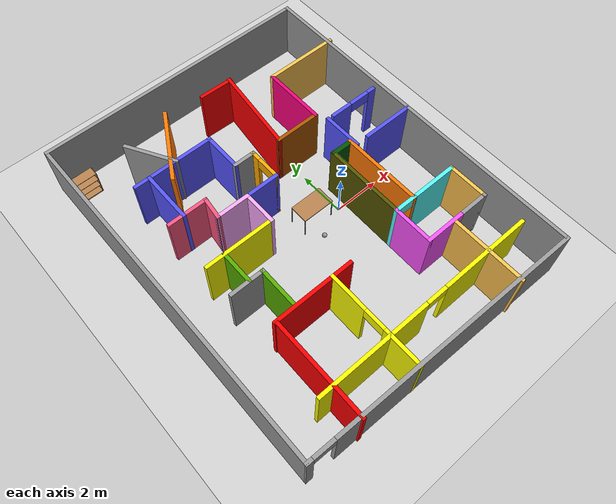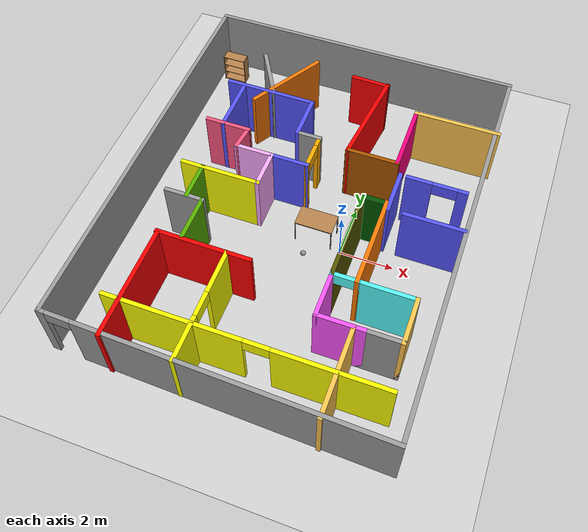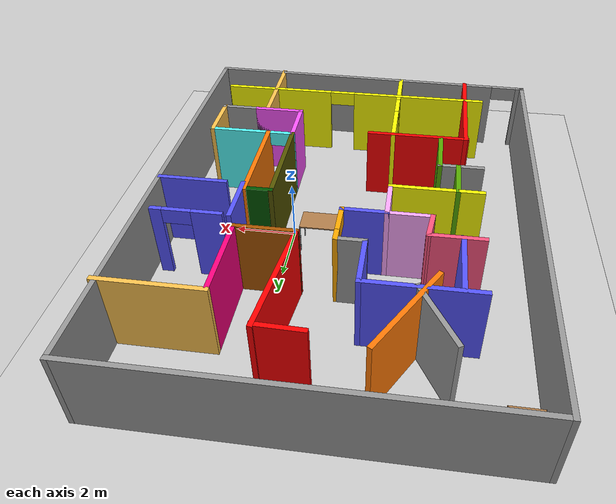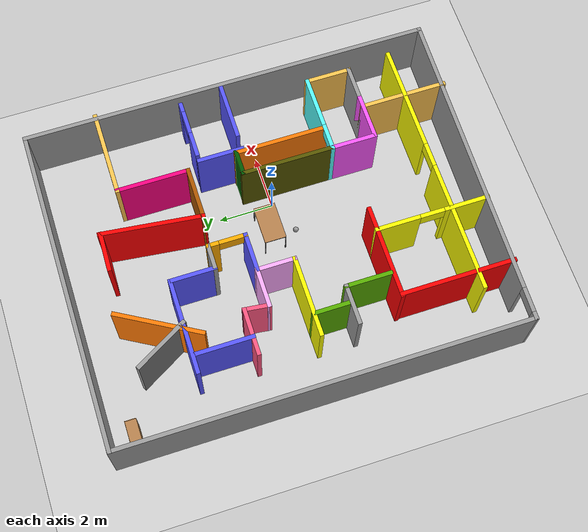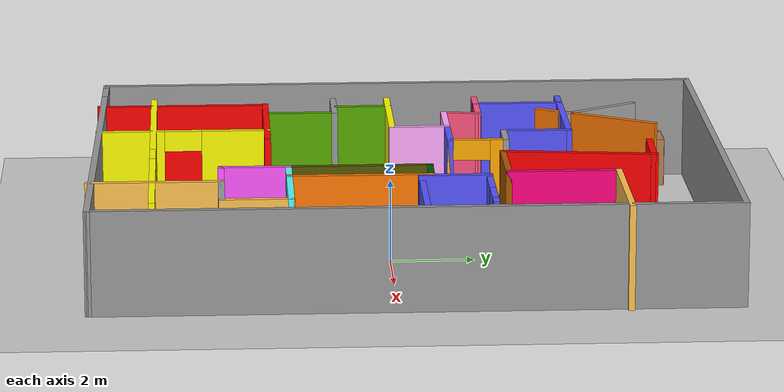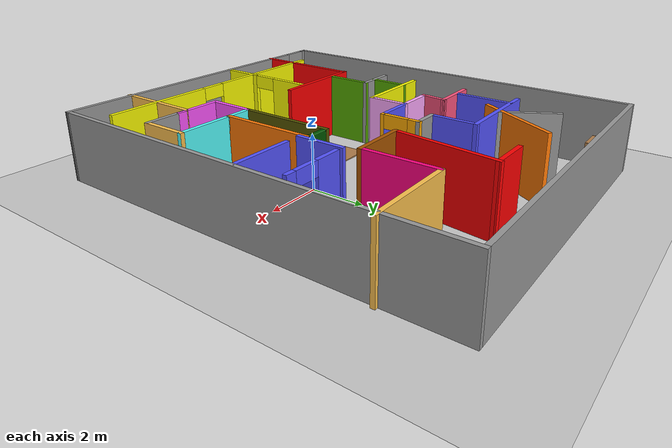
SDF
<sdf version="1.6">
 <world name="default">
  <light name="sun" type="directional">
   <pose>0 0 10 0 -0 0</pose>
   <diffuse>0.8 0.8 0.8 1</diffuse>
   <specular>0.1 0.1 0.1 1</specular>
   <attenuation>
    <range>1000</range>
    <constant>0.9</constant>
    <linear>0.01</linear>
    <quadratic>0.001</quadratic>
   </attenuation>
   <direction>-0.5 0.5 -1</direction>
  </light>
  <model name="ground_plane">
   <static>1</static>
   <link name="link">
    <collision name="collision">
     <geometry><plane><normal>0 0 1</normal><size>100 100</size></plane></geometry>
     <surface><friction><ode><mu>100</mu><mu2>50</mu2></ode></friction></surface>
    </collision>
    <visual name="visual">
     <cast_shadows>0</cast_shadows>
     <geometry><plane><normal>0 0 1</normal><size>100 100</size></plane></geometry>
     <material>
      <script><uri>file://media/materials/scripts/gazebo.material</uri><name>Gazebo/Grey</name></script>
     </material>
    </visual>
   </link>
  </model>
  <gravity>0 0 -9.8</gravity>
  <magnetic_field>6e-06 2.3e-05 -4.2e-05</magnetic_field>
  <atmosphere type="adiabatic"/>
  <physics name="default_physics" default="0" type="ode">
   <max_step_size>0.001</max_step_size>
   <real_time_factor>1</real_time_factor>
   <real_time_update_rate>1000</real_time_update_rate>
  </physics>
  <scene><ambient>0.4 0.4 0.4 1</ambient><background>0.7 0.7 0.7 1</background><shadows>1</shadows></scene>
  <spherical_coordinates>
   <surface_model>EARTH_WGS84</surface_model>
   <latitude_deg>0</latitude_deg>
   <longitude_deg>0</longitude_deg>
   <elevation>0</elevation>
   <heading_deg>0</heading_deg>
  </spherical_coordinates>
  <model name="try_example">
   <link name="Wall_1">
    <pose>-5.97854 0.156676 0 0 -0 1.5708</pose>
    <visual name="Wall_1_Visual">
     <pose>0 0 1.25 0 -0 0</pose>
     <geometry><box><size>14.9191 0.15 2.5</size></box></geometry>
     <material>
      <script><uri>file://media/materials/scripts/gazebo.material</uri><name>Gazebo/Grey</name></script>
      <ambient>0 0 0 1</ambient>
      <diffuse>0.7 0.7 0.7 1</diffuse>
      <specular>0.01 0.01 0.01 1</specular>
      <emissive>0 0 0 1</emissive>
     </material>
    </visual>
    <collision name="Wall_1_Collision">
     <pose>0 0 1.25 0 -0 0</pose>
     <geometry><box><size>14.9191 0.15 2.5</size></box></geometry>
     <surface>
      <friction>
       <ode><mu>1</mu><mu2>1</mu2><fdir1>0 0 0</fdir1><slip1>0</slip1><slip2>0</slip2></ode>
       <torsional>
        <coefficient>1</coefficient>
        <patch_radius>0</patch_radius>
        <surface_radius>0</surface_radius>
        <use_patch_radius>1</use_patch_radius>
        <ode><slip>0</slip></ode>
       </torsional>
      </friction>
      <bounce><restitution_coefficient>0</restitution_coefficient><threshold>1e+06</threshold></bounce>
      <contact>
       <collide_without_contact>0</collide_without_contact>
       <collide_without_contact_bitmask>1</collide_without_contact_bitmask>
       <collide_bitmask>1</collide_bitmask>
       <ode>
        <soft_cfm>0</soft_cfm>
        <soft_erp>0.2</soft_erp>
        <kp>1e+13</kp>
        <kd>1</kd>
        <max_vel>0.01</max_vel>
        <min_depth>0</min_depth>
       </ode>
       <bullet>
        <split_impulse>1</split_impulse>
        <split_impulse_penetration_threshold>-0.01</split_impulse_penetration_threshold>
        <soft_cfm>0</soft_cfm>
        <soft_erp>0.2</soft_erp>
        <kp>1e+13</kp>
        <kd>1</kd>
       </bullet>
      </contact>
     </surface>
    </collision>
   </link>
   <link name="Wall_11">
    <pose>4.4301 4.9191 0 0 -0 3.14159</pose>
    <visual name="Wall_11_Visual">
     <pose>0 0 1.25 0 -0 0</pose>
     <geometry><box><size>3.25 0.15 2.5</size></box></geometry>
     <material>
      <script><uri>file://media/materials/scripts/gazebo.material</uri><name>Gazebo/Grey</name></script>
      <ambient>1 0.764706 0.305882 1</ambient>
      <diffuse>0.7 0.7 0.7 1</diffuse>
      <specular>0.01 0.01 0.01 1</specular>
      <emissive>0 0 0 1</emissive>
     </material>
    </visual>
    <collision name="Wall_11_Collision">
     <pose>0 0 1.25 0 -0 0</pose>
     <geometry><box><size>3.25 0.15 2.5</size></box></geometry>
     <surface>
      <friction>
       <ode><mu>1</mu><mu2>1</mu2><fdir1>0 0 0</fdir1><slip1>0</slip1><slip2>0</slip2></ode>
       <torsional>
        <coefficient>1</coefficient>
        <patch_radius>0</patch_radius>
        <surface_radius>0</surface_radius>
        <use_patch_radius>1</use_patch_radius>
        <ode><slip>0</slip></ode>
       </torsional>
      </friction>
      <bounce><restitution_coefficient>0</restitution_coefficient><threshold>1e+06</threshold></bounce>
      <contact>
       <collide_without_contact>0</collide_without_contact>
       <collide_without_contact_bitmask>1</collide_without_contact_bitmask>
       <collide_bitmask>1</collide_bitmask>
       <ode>
        <soft_cfm>0</soft_cfm>
        <soft_erp>0.2</soft_erp>
        <kp>1e+13</kp>
        <kd>1</kd>
        <max_vel>0.01</max_vel>
        <min_depth>0</min_depth>
       </ode>
       <bullet>
        <split_impulse>1</split_impulse>
        <split_impulse_penetration_threshold>-0.01</split_impulse_penetration_threshold>
        <soft_cfm>0</soft_cfm>
        <soft_erp>0.2</soft_erp>
        <kp>1e+13</kp>
        <kd>1</kd>
       </bullet>
      </contact>
     </surface>
    </collision>
   </link>
   <link name="Wall_12">
    <pose>2.8801 3.6191 0 0 0 -1.5708</pose>
    <visual name="Wall_12_Visual">
     <pose>0 0 1.25 0 -0 0</pose>
     <geometry><box><size>2.75 0.15 2.5</size></box></geometry>
     <material>
      <script><uri>file://media/materials/scripts/gazebo.material</uri><name>Gazebo/Grey</name></script>
      <ambient>1 0 0.498039 1</ambient>
      <diffuse>0.7 0.7 0.7 1</diffuse>
      <specular>0.01 0.01 0.01 1</specular>
      <emissive>0 0 0 1</emissive>
     </material>
    </visual>
    <collision name="Wall_12_Collision">
     <pose>0 0 1.25 0 -0 0</pose>
     <geometry><box><size>2.75 0.15 2.5</size></box></geometry>
     <surface>
      <friction>
       <ode><mu>1</mu><mu2>1</mu2><fdir1>0 0 0</fdir1><slip1>0</slip1><slip2>0</slip2></ode>
       <torsional>
        <coefficient>1</coefficient>
        <patch_radius>0</patch_radius>
        <surface_radius>0</surface_radius>
        <use_patch_radius>1</use_patch_radius>
        <ode><slip>0</slip></ode>
       </torsional>
      </friction>
      <bounce><restitution_coefficient>0</restitution_coefficient><threshold>1e+06</threshold></bounce>
      <contact>
       <collide_without_contact>0</collide_without_contact>
       <collide_without_contact_bitmask>1</collide_without_contact_bitmask>
       <collide_bitmask>1</collide_bitmask>
       <ode>
        <soft_cfm>0</soft_cfm>
        <soft_erp>0.2</soft_erp>
        <kp>1e+13</kp>
        <kd>1</kd>
        <max_vel>0.01</max_vel>
        <min_depth>0</min_depth>
       </ode>
       <bullet>
        <split_impulse>1</split_impulse>
        <split_impulse_penetration_threshold>-0.01</split_impulse_penetration_threshold>
        <soft_cfm>0</soft_cfm>
        <soft_erp>0.2</soft_erp>
        <kp>1e+13</kp>
        <kd>1</kd>
       </bullet>
      </contact>
     </surface>
    </collision>
   </link>
   <link name="Wall_13">
    <pose>1.9551 2.3191 0 0 -0 3.14159</pose>
    <visual name="Wall_13_Visual">
     <pose>0 0 1.25 0 -0 0</pose>
     <geometry><box><size>2 0.15 2.5</size></box></geometry>
     <material>
      <script><uri>file://media/materials/scripts/gazebo.material</uri><name>Gazebo/Grey</name></script>
      <ambient>0.666667 0.333333 0 1</ambient>
      <diffuse>0.7 0.7 0.7 1</diffuse>
      <specular>0.01 0.01 0.01 1</specular>
      <emissive>0 0 0 1</emissive>
     </material>
    </visual>
    <collision name="Wall_13_Collision">
     <pose>0 0 1.25 0 -0 0</pose>
     <geometry><box><size>2 0.15 2.5</size></box></geometry>
     <surface>
      <friction>
       <ode><mu>1</mu><mu2>1</mu2><fdir1>0 0 0</fdir1><slip1>0</slip1><slip2>0</slip2></ode>
       <torsional>
        <coefficient>1</coefficient>
        <patch_radius>0</patch_radius>
        <surface_radius>0</surface_radius>
        <use_patch_radius>1</use_patch_radius>
        <ode><slip>0</slip></ode>
       </torsional>
      </friction>
      <bounce><restitution_coefficient>0</restitution_coefficient><threshold>1e+06</threshold></bounce>
      <contact>
       <collide_without_contact>0</collide_without_contact>
       <collide_without_contact_bitmask>1</collide_without_contact_bitmask>
       <collide_bitmask>1</collide_bitmask>
       <ode>
        <soft_cfm>0</soft_cfm>
        <soft_erp>0.2</soft_erp>
        <kp>1e+13</kp>
        <kd>1</kd>
        <max_vel>0.01</max_vel>
        <min_depth>0</min_depth>
       </ode>
       <bullet>
        <split_impulse>1</split_impulse>
        <split_impulse_penetration_threshold>-0.01</split_impulse_penetration_threshold>
        <soft_cfm>0</soft_cfm>
        <soft_erp>0.2</soft_erp>
        <kp>1e+13</kp>
        <kd>1</kd>
       </bullet>
      </contact>
     </surface>
    </collision>
   </link>
   <link name="Wall_14">
    <pose>1.24117 4.12732 0 0 -0 1.45459</pose>
    <visual name="Wall_14_Visual">
     <pose>0 0 1.25 0 -0 0</pose>
     <geometry><box><size>3.79099 0.15 2.5</size></box></geometry>
     <material>
      <script><uri>file://media/materials/scripts/gazebo.material</uri><name>Gazebo/Grey</name></script>
      <ambient>1 0 0 1</ambient>
      <diffuse>0.7 0.7 0.7 1</diffuse>
      <specular>0.01 0.01 0.01 1</specular>
      <emissive>0 0 0 1</emissive>
     </material>
    </visual>
    <collision name="Wall_14_Collision">
     <pose>0 0 1.25 0 -0 0</pose>
     <geometry><box><size>3.79099 0.15 2.5</size></box></geometry>
     <surface>
      <friction>
       <ode><mu>1</mu><mu2>1</mu2><fdir1>0 0 0</fdir1><slip1>0</slip1><slip2>0</slip2></ode>
       <torsional>
        <coefficient>1</coefficient>
        <patch_radius>0</patch_radius>
        <surface_radius>0</surface_radius>
        <use_patch_radius>1</use_patch_radius>
        <ode><slip>0</slip></ode>
       </torsional>
      </friction>
      <bounce><restitution_coefficient>0</restitution_coefficient><threshold>1e+06</threshold></bounce>
      <contact>
       <collide_without_contact>0</collide_without_contact>
       <collide_without_contact_bitmask>1</collide_without_contact_bitmask>
       <collide_bitmask>1</collide_bitmask>
       <ode>
        <soft_cfm>0</soft_cfm>
        <soft_erp>0.2</soft_erp>
        <kp>1e+13</kp>
        <kd>1</kd>
        <max_vel>0.01</max_vel>
        <min_depth>0</min_depth>
       </ode>
       <bullet>
        <split_impulse>1</split_impulse>
        <split_impulse_penetration_threshold>-0.01</split_impulse_penetration_threshold>
        <soft_cfm>0</soft_cfm>
        <soft_erp>0.2</soft_erp>
        <kp>1e+13</kp>
        <kd>1</kd>
       </bullet>
      </contact>
     </surface>
    </collision>
   </link>
   <link name="Wall_15">
    <pose>0.777248 5.91794 0 0 -0 3.11554</pose>
    <visual name="Wall_15_Visual">
     <pose>0 0 1.25 0 -0 0</pose>
     <geometry><box><size>1.50046 0.15 2.5</size></box></geometry>
     <material>
      <script><uri>file://media/materials/scripts/gazebo.material</uri><name>Gazebo/Grey</name></script>
      <ambient>1 0 0 1</ambient>
      <diffuse>0.7 0.7 0.7 1</diffuse>
      <specular>0.01 0.01 0.01 1</specular>
      <emissive>0 0 0 1</emissive>
     </material>
    </visual>
    <collision name="Wall_15_Collision">
     <pose>0 0 1.25 0 -0 0</pose>
     <geometry><box><size>1.50046 0.15 2.5</size></box></geometry>
     <surface>
      <friction>
       <ode><mu>1</mu><mu2>1</mu2><fdir1>0 0 0</fdir1><slip1>0</slip1><slip2>0</slip2></ode>
       <torsional>
        <coefficient>1</coefficient>
        <patch_radius>0</patch_radius>
        <surface_radius>0</surface_radius>
        <use_patch_radius>1</use_patch_radius>
        <ode><slip>0</slip></ode>
       </torsional>
      </friction>
      <bounce><restitution_coefficient>0</restitution_coefficient><threshold>1e+06</threshold></bounce>
      <contact>
       <collide_without_contact>0</collide_without_contact>
       <collide_without_contact_bitmask>1</collide_without_contact_bitmask>
       <collide_bitmask>1</collide_bitmask>
       <ode>
        <soft_cfm>0</soft_cfm>
        <soft_erp>0.2</soft_erp>
        <kp>1e+13</kp>
        <kd>1</kd>
        <max_vel>0.01</max_vel>
        <min_depth>0</min_depth>
       </ode>
       <bullet>
        <split_impulse>1</split_impulse>
        <split_impulse_penetration_threshold>-0.01</split_impulse_penetration_threshold>
        <soft_cfm>0</soft_cfm>
        <soft_erp>0.2</soft_erp>
        <kp>1e+13</kp>
        <kd>1</kd>
       </bullet>
      </contact>
     </surface>
    </collision>
   </link>
   <link name="Wall_17">
    <pose>4.45382 1.83901 0 0 -0 3.14159</pose>
    <visual name="Wall_17_Visual_0">
     <pose>-0.934537 0 1.25 0 -0 0</pose>
     <geometry><box><size>0.380925 0.15 2.5</size></box></geometry>
     <material>
      <script><uri>file://media/materials/scripts/gazebo.material</uri><name>Gazebo/Grey</name></script>
      <ambient>0.333333 0.333333 1 1</ambient>
      <diffuse>0.7 0.7 0.7 1</diffuse>
      <specular>0.01 0.01 0.01 1</specular>
      <emissive>0 0 0 1</emissive>
     </material>
    </visual>
    <visual name="Wall_17_Visual_1">
     <pose>0.640463 0 1.25 0 -0 0</pose>
     <geometry><box><size>0.969075 0.15 2.5</size></box></geometry>
     <material>
      <script><uri>file://media/materials/scripts/gazebo.material</uri><name>Gazebo/Grey</name></script>
      <ambient>0.333333 0.333333 1 1</ambient>
      <diffuse>0.7 0.7 0.7 1</diffuse>
      <specular>0.01 0.01 0.01 1</specular>
      <emissive>0 0 0 1</emissive>
     </material>
    </visual>
    <visual name="Wall_17_Visual_2">
     <pose>-0.294075 0 2.25 0 -0 0</pose>
     <geometry><box><size>0.9 0.15 0.5</size></box></geometry>
     <material>
      <script><uri>file://media/materials/scripts/gazebo.material</uri><name>Gazebo/Grey</name></script>
      <ambient>0.333333 0.333333 1 1</ambient>
      <diffuse>0.7 0.7 0.7 1</diffuse>
      <specular>0.01 0.01 0.01 1</specular>
      <emissive>0 0 0 1</emissive>
     </material>
    </visual>
    <collision name="Wall_17_Collision_0">
     <pose>-0.934537 0 1.25 0 -0 0</pose>
     <geometry><box><size>0.380925 0.15 2.5</size></box></geometry>
     <surface>
      <friction>
       <ode><mu>1</mu><mu2>1</mu2><fdir1>0 0 0</fdir1><slip1>0</slip1><slip2>0</slip2></ode>
       <torsional>
        <coefficient>1</coefficient>
        <patch_radius>0</patch_radius>
        <surface_radius>0</surface_radius>
        <use_patch_radius>1</use_patch_radius>
        <ode><slip>0</slip></ode>
       </torsional>
      </friction>
      <bounce><restitution_coefficient>0</restitution_coefficient><threshold>1e+06</threshold></bounce>
      <contact>
       <collide_without_contact>0</collide_without_contact>
       <collide_without_contact_bitmask>1</collide_without_contact_bitmask>
       <collide_bitmask>1</collide_bitmask>
       <ode>
        <soft_cfm>0</soft_cfm>
        <soft_erp>0.2</soft_erp>
        <kp>1e+13</kp>
        <kd>1</kd>
        <max_vel>0.01</max_vel>
        <min_depth>0</min_depth>
       </ode>
       <bullet>
        <split_impulse>1</split_impulse>
        <split_impulse_penetration_threshold>-0.01</split_impulse_penetration_threshold>
        <soft_cfm>0</soft_cfm>
        <soft_erp>0.2</soft_erp>
        <kp>1e+13</kp>
        <kd>1</kd>
       </bullet>
      </contact>
     </surface>
    </collision>
    <collision name="Wall_17_Collision_1">
     <pose>0.640463 0 1.25 0 -0 0</pose>
     <geometry><box><size>0.969075 0.15 2.5</size></box></geometry>
     <surface>
      <friction>
       <ode><mu>1</mu><mu2>1</mu2><fdir1>0 0 0</fdir1><slip1>0</slip1><slip2>0</slip2></ode>
       <torsional>
        <coefficient>1</coefficient>
        <patch_radius>0</patch_radius>
        <surface_radius>0</surface_radius>
        <use_patch_radius>1</use_patch_radius>
        <ode><slip>0</slip></ode>
       </torsional>
      </friction>
      <bounce><restitution_coefficient>0</restitution_coefficient><threshold>1e+06</threshold></bounce>
      <contact>
       <collide_without_contact>0</collide_without_contact>
       <collide_without_contact_bitmask>1</collide_without_contact_bitmask>
       <collide_bitmask>1</collide_bitmask>
       <ode>
        <soft_cfm>0</soft_cfm>
        <soft_erp>0.2</soft_erp>
        <kp>1e+13</kp>
        <kd>1</kd>
        <max_vel>0.01</max_vel>
        <min_depth>0</min_depth>
       </ode>
       <bullet>
        <split_impulse>1</split_impulse>
        <split_impulse_penetration_threshold>-0.01</split_impulse_penetration_threshold>
        <soft_cfm>0</soft_cfm>
        <soft_erp>0.2</soft_erp>
        <kp>1e+13</kp>
        <kd>1</kd>
       </bullet>
      </contact>
     </surface>
    </collision>
    <collision name="Wall_17_Collision_2">
     <pose>-0.294075 0 2.25 0 -0 0</pose>
     <geometry><box><size>0.9 0.15 0.5</size></box></geometry>
     <surface>
      <friction>
       <ode><mu>1</mu><mu2>1</mu2><fdir1>0 0 0</fdir1><slip1>0</slip1><slip2>0</slip2></ode>
       <torsional>
        <coefficient>1</coefficient>
        <patch_radius>0</patch_radius>
        <surface_radius>0</surface_radius>
        <use_patch_radius>1</use_patch_radius>
        <ode><slip>0</slip></ode>
       </torsional>
      </friction>
      <bounce><restitution_coefficient>0</restitution_coefficient><threshold>1e+06</threshold></bounce>
      <contact>
       <collide_without_contact>0</collide_without_contact>
       <collide_without_contact_bitmask>1</collide_without_contact_bitmask>
       <collide_bitmask>1</collide_bitmask>
       <ode>
        <soft_cfm>0</soft_cfm>
        <soft_erp>0.2</soft_erp>
        <kp>1e+13</kp>
        <kd>1</kd>
        <max_vel>0.01</max_vel>
        <min_depth>0</min_depth>
       </ode>
       <bullet>
        <split_impulse>1</split_impulse>
        <split_impulse_penetration_threshold>-0.01</split_impulse_penetration_threshold>
        <soft_cfm>0</soft_cfm>
        <soft_erp>0.2</soft_erp>
        <kp>1e+13</kp>
        <kd>1</kd>
       </bullet>
      </contact>
     </surface>
    </collision>
   </link>
   <link name="Wall_18">
    <pose>3.13064 1.04811 0 0 0 -1.5708</pose>
    <visual name="Wall_18_Visual">
     <pose>0 0 1.25 0 -0 0</pose>
     <geometry><box><size>1.75 0.15 2.5</size></box></geometry>
     <material>
      <script><uri>file://media/materials/scripts/gazebo.material</uri><name>Gazebo/Grey</name></script>
      <ambient>0.333333 0.333333 1 1</ambient>
      <diffuse>0.7 0.7 0.7 1</diffuse>
      <specular>0.01 0.01 0.01 1</specular>
      <emissive>0 0 0 1</emissive>
     </material>
    </visual>
    <collision name="Wall_18_Collision">
     <pose>0 0 1.25 0 -0 0</pose>
     <geometry><box><size>1.75 0.15 2.5</size></box></geometry>
     <surface>
      <friction>
       <ode><mu>1</mu><mu2>1</mu2><fdir1>0 0 0</fdir1><slip1>0</slip1><slip2>0</slip2></ode>
       <torsional>
        <coefficient>1</coefficient>
        <patch_radius>0</patch_radius>
        <surface_radius>0</surface_radius>
        <use_patch_radius>1</use_patch_radius>
        <ode><slip>0</slip></ode>
       </torsional>
      </friction>
      <bounce><restitution_coefficient>0</restitution_coefficient><threshold>1e+06</threshold></bounce>
      <contact>
       <collide_without_contact>0</collide_without_contact>
       <collide_without_contact_bitmask>1</collide_without_contact_bitmask>
       <collide_bitmask>1</collide_bitmask>
       <ode>
        <soft_cfm>0</soft_cfm>
        <soft_erp>0.2</soft_erp>
        <kp>1e+13</kp>
        <kd>1</kd>
        <max_vel>0.01</max_vel>
        <min_depth>0</min_depth>
       </ode>
       <bullet>
        <split_impulse>1</split_impulse>
        <split_impulse_penetration_threshold>-0.01</split_impulse_penetration_threshold>
        <soft_cfm>0</soft_cfm>
        <soft_erp>0.2</soft_erp>
        <kp>1e+13</kp>
        <kd>1</kd>
       </bullet>
      </contact>
     </surface>
    </collision>
   </link>
   <link name="Wall_24">
    <pose>4.76828 0.244473 0 0 -0 0</pose>
    <visual name="Wall_24_Visual">
     <pose>0 0 1.25 0 -0 0</pose>
     <geometry><box><size>2.25 0.15 2.5</size></box></geometry>
     <material>
      <script><uri>file://media/materials/scripts/gazebo.material</uri><name>Gazebo/Grey</name></script>
      <ambient>0.333333 0.333333 1 1</ambient>
      <diffuse>0.7 0.7 0.7 1</diffuse>
      <specular>0.01 0.01 0.01 1</specular>
      <emissive>0 0 0 1</emissive>
     </material>
    </visual>
    <collision name="Wall_24_Collision">
     <pose>0 0 1.25 0 -0 0</pose>
     <geometry><box><size>2.25 0.15 2.5</size></box></geometry>
     <surface>
      <friction>
       <ode><mu>1</mu><mu2>1</mu2><fdir1>0 0 0</fdir1><slip1>0</slip1><slip2>0</slip2></ode>
       <torsional>
        <coefficient>1</coefficient>
        <patch_radius>0</patch_radius>
        <surface_radius>0</surface_radius>
        <use_patch_radius>1</use_patch_radius>
        <ode><slip>0</slip></ode>
       </torsional>
      </friction>
      <bounce><restitution_coefficient>0</restitution_coefficient><threshold>1e+06</threshold></bounce>
      <contact>
       <collide_without_contact>0</collide_without_contact>
       <collide_without_contact_bitmask>1</collide_without_contact_bitmask>
       <collide_bitmask>1</collide_bitmask>
       <ode>
        <soft_cfm>0</soft_cfm>
        <soft_erp>0.2</soft_erp>
        <kp>1e+13</kp>
        <kd>1</kd>
        <max_vel>0.01</max_vel>
        <min_depth>0</min_depth>
       </ode>
       <bullet>
        <split_impulse>1</split_impulse>
        <split_impulse_penetration_threshold>-0.01</split_impulse_penetration_threshold>
        <soft_cfm>0</soft_cfm>
        <soft_erp>0.2</soft_erp>
        <kp>1e+13</kp>
        <kd>1</kd>
       </bullet>
      </contact>
     </surface>
    </collision>
   </link>
   <link name="Wall_26">
    <pose>-2.96058 -2.37202 0 0 -0 1.5708</pose>
    <visual name="Wall_26_Visual">
     <pose>0 0 1.25 0 -0 0</pose>
     <geometry><box><size>1.75 0.15 2.5</size></box></geometry>
     <material>
      <script><uri>file://media/materials/scripts/gazebo.material</uri><name>Gazebo/Grey</name></script>
      <ambient>0.333333 0.666667 0 1</ambient>
      <diffuse>0.7 0.7 0.7 1</diffuse>
      <specular>0.01 0.01 0.01 1</specular>
      <emissive>0 0 0 1</emissive>
     </material>
    </visual>
    <collision name="Wall_26_Collision">
     <pose>0 0 1.25 0 -0 0</pose>
     <geometry><box><size>1.75 0.15 2.5</size></box></geometry>
     <surface>
      <friction>
       <ode><mu>1</mu><mu2>1</mu2><fdir1>0 0 0</fdir1><slip1>0</slip1><slip2>0</slip2></ode>
       <torsional>
        <coefficient>1</coefficient>
        <patch_radius>0</patch_radius>
        <surface_radius>0</surface_radius>
        <use_patch_radius>1</use_patch_radius>
        <ode><slip>0</slip></ode>
       </torsional>
      </friction>
      <bounce><restitution_coefficient>0</restitution_coefficient><threshold>1e+06</threshold></bounce>
      <contact>
       <collide_without_contact>0</collide_without_contact>
       <collide_without_contact_bitmask>1</collide_without_contact_bitmask>
       <collide_bitmask>1</collide_bitmask>
       <ode>
        <soft_cfm>0</soft_cfm>
        <soft_erp>0.2</soft_erp>
        <kp>1e+13</kp>
        <kd>1</kd>
        <max_vel>0.01</max_vel>
        <min_depth>0</min_depth>
       </ode>
       <bullet>
        <split_impulse>1</split_impulse>
        <split_impulse_penetration_threshold>-0.01</split_impulse_penetration_threshold>
        <soft_cfm>0</soft_cfm>
        <soft_erp>0.2</soft_erp>
        <kp>1e+13</kp>
        <kd>1</kd>
       </bullet>
      </contact>
     </surface>
    </collision>
   </link>
   <link name="Wall_27">
    <pose>-3.63558 -1.57202 0 0 -0 3.14159</pose>
    <visual name="Wall_27_Visual">
     <pose>0 0 1.25 0 -0 0</pose>
     <geometry><box><size>1.5 0.15 2.5</size></box></geometry>
     <material>
      <script><uri>file://media/materials/scripts/gazebo.material</uri><name>Gazebo/Grey</name></script>
      <ambient>1 1 1 1</ambient>
      <diffuse>0.7 0.7 0.7 1</diffuse>
      <specular>0.01 0.01 0.01 1</specular>
      <emissive>0 0 0 1</emissive>
     </material>
    </visual>
    <collision name="Wall_27_Collision">
     <pose>0 0 1.25 0 -0 0</pose>
     <geometry><box><size>1.5 0.15 2.5</size></box></geometry>
     <surface>
      <friction>
       <ode><mu>1</mu><mu2>1</mu2><fdir1>0 0 0</fdir1><slip1>0</slip1><slip2>0</slip2></ode>
       <torsional>
        <coefficient>1</coefficient>
        <patch_radius>0</patch_radius>
        <surface_radius>0</surface_radius>
        <use_patch_radius>1</use_patch_radius>
        <ode><slip>0</slip></ode>
       </torsional>
      </friction>
      <bounce><restitution_coefficient>0</restitution_coefficient><threshold>1e+06</threshold></bounce>
      <contact>
       <collide_without_contact>0</collide_without_contact>
       <collide_without_contact_bitmask>1</collide_without_contact_bitmask>
       <collide_bitmask>1</collide_bitmask>
       <ode>
        <soft_cfm>0</soft_cfm>
        <soft_erp>0.2</soft_erp>
        <kp>1e+13</kp>
        <kd>1</kd>
        <max_vel>0.01</max_vel>
        <min_depth>0</min_depth>
       </ode>
       <bullet>
        <split_impulse>1</split_impulse>
        <split_impulse_penetration_threshold>-0.01</split_impulse_penetration_threshold>
        <soft_cfm>0</soft_cfm>
        <soft_erp>0.2</soft_erp>
        <kp>1e+13</kp>
        <kd>1</kd>
       </bullet>
      </contact>
     </surface>
    </collision>
   </link>
   <link name="Wall_28">
    <pose>-3.55189 -0.897016 0 0 -0 1.5708</pose>
    <visual name="Wall_28_Visual">
     <pose>0 0 1.25 0 -0 0</pose>
     <geometry><box><size>1.5 0.15 2.5</size></box></geometry>
     <material>
      <script><uri>file://media/materials/scripts/gazebo.material</uri><name>Gazebo/Grey</name></script>
      <ambient>0.333333 0.666667 0 1</ambient>
      <diffuse>0.7 0.7 0.7 1</diffuse>
      <specular>0.01 0.01 0.01 1</specular>
      <emissive>0 0 0 1</emissive>
     </material>
    </visual>
    <collision name="Wall_28_Collision">
     <pose>0 0 1.25 0 -0 0</pose>
     <geometry><box><size>1.5 0.15 2.5</size></box></geometry>
     <surface>
      <friction>
       <ode><mu>1</mu><mu2>1</mu2><fdir1>0 0 0</fdir1><slip1>0</slip1><slip2>0</slip2></ode>
       <torsional>
        <coefficient>1</coefficient>
        <patch_radius>0</patch_radius>
        <surface_radius>0</surface_radius>
        <use_patch_radius>1</use_patch_radius>
        <ode><slip>0</slip></ode>
       </torsional>
      </friction>
      <bounce><restitution_coefficient>0</restitution_coefficient><threshold>1e+06</threshold></bounce>
      <contact>
       <collide_without_contact>0</collide_without_contact>
       <collide_without_contact_bitmask>1</collide_without_contact_bitmask>
       <collide_bitmask>1</collide_bitmask>
       <ode>
        <soft_cfm>0</soft_cfm>
        <soft_erp>0.2</soft_erp>
        <kp>1e+13</kp>
        <kd>1</kd>
        <max_vel>0.01</max_vel>
        <min_depth>0</min_depth>
       </ode>
       <bullet>
        <split_impulse>1</split_impulse>
        <split_impulse_penetration_threshold>-0.01</split_impulse_penetration_threshold>
        <soft_cfm>0</soft_cfm>
        <soft_erp>0.2</soft_erp>
        <kp>1e+13</kp>
        <kd>1</kd>
       </bullet>
      </contact>
     </surface>
    </collision>
   </link>
   <link name="Wall_29">
    <pose>-2.88558 -0.222018 0 0 -0 0</pose>
    <visual name="Wall_29_Visual">
     <pose>0 0 1.25 0 -0 0</pose>
     <geometry><box><size>3 0.15 2.5</size></box></geometry>
     <material>
      <script><uri>file://media/materials/scripts/gazebo.material</uri><name>Gazebo/Grey</name></script>
      <ambient>1 1 0 1</ambient>
      <diffuse>0.7 0.7 0.7 1</diffuse>
      <specular>0.01 0.01 0.01 1</specular>
      <emissive>0 0 0 1</emissive>
     </material>
    </visual>
    <collision name="Wall_29_Collision">
     <pose>0 0 1.25 0 -0 0</pose>
     <geometry><box><size>3 0.15 2.5</size></box></geometry>
     <surface>
      <friction>
       <ode><mu>1</mu><mu2>1</mu2><fdir1>0 0 0</fdir1><slip1>0</slip1><slip2>0</slip2></ode>
       <torsional>
        <coefficient>1</coefficient>
        <patch_radius>0</patch_radius>
        <surface_radius>0</surface_radius>
        <use_patch_radius>1</use_patch_radius>
        <ode><slip>0</slip></ode>
       </torsional>
      </friction>
      <bounce><restitution_coefficient>0</restitution_coefficient><threshold>1e+06</threshold></bounce>
      <contact>
       <collide_without_contact>0</collide_without_contact>
       <collide_without_contact_bitmask>1</collide_without_contact_bitmask>
       <collide_bitmask>1</collide_bitmask>
       <ode>
        <soft_cfm>0</soft_cfm>
        <soft_erp>0.2</soft_erp>
        <kp>1e+13</kp>
        <kd>1</kd>
        <max_vel>0.01</max_vel>
        <min_depth>0</min_depth>
       </ode>
       <bullet>
        <split_impulse>1</split_impulse>
        <split_impulse_penetration_threshold>-0.01</split_impulse_penetration_threshold>
        <soft_cfm>0</soft_cfm>
        <soft_erp>0.2</soft_erp>
        <kp>1e+13</kp>
        <kd>1</kd>
       </bullet>
      </contact>
     </surface>
    </collision>
   </link>
   <link name="Wall_3">
    <pose>-0.053538 7.54122 0 0 -0 0</pose>
    <visual name="Wall_3_Visual">
     <pose>0 0 1.25 0 -0 0</pose>
     <geometry><box><size>12 0.15 2.5</size></box></geometry>
     <material>
      <script><uri>file://media/materials/scripts/gazebo.material</uri><name>Gazebo/Grey</name></script>
      <ambient>0 0 0 1</ambient>
      <diffuse>0.7 0.7 0.7 1</diffuse>
      <specular>0.01 0.01 0.01 1</specular>
      <emissive>0 0 0 1</emissive>
     </material>
    </visual>
    <collision name="Wall_3_Collision">
     <pose>0 0 1.25 0 -0 0</pose>
     <geometry><box><size>12 0.15 2.5</size></box></geometry>
     <surface>
      <friction>
       <ode><mu>1</mu><mu2>1</mu2><fdir1>0 0 0</fdir1><slip1>0</slip1><slip2>0</slip2></ode>
       <torsional>
        <coefficient>1</coefficient>
        <patch_radius>0</patch_radius>
        <surface_radius>0</surface_radius>
        <use_patch_radius>1</use_patch_radius>
        <ode><slip>0</slip></ode>
       </torsional>
      </friction>
      <bounce><restitution_coefficient>0</restitution_coefficient><threshold>1e+06</threshold></bounce>
      <contact>
       <collide_without_contact>0</collide_without_contact>
       <collide_without_contact_bitmask>1</collide_without_contact_bitmask>
       <collide_bitmask>1</collide_bitmask>
       <ode>
        <soft_cfm>0</soft_cfm>
        <soft_erp>0.2</soft_erp>
        <kp>1e+13</kp>
        <kd>1</kd>
        <max_vel>0.01</max_vel>
        <min_depth>0</min_depth>
       </ode>
       <bullet>
        <split_impulse>1</split_impulse>
        <split_impulse_penetration_threshold>-0.01</split_impulse_penetration_threshold>
        <soft_cfm>0</soft_cfm>
        <soft_erp>0.2</soft_erp>
        <kp>1e+13</kp>
        <kd>1</kd>
       </bullet>
      </contact>
     </surface>
    </collision>
   </link>
   <link name="Wall_30">
    <pose>-1.46058 0.452981 0 0 -0 1.5708</pose>
    <visual name="Wall_30_Visual">
     <pose>0 0 1.25 0 -0 0</pose>
     <geometry><box><size>1.5 0.15 2.5</size></box></geometry>
     <material>
      <script><uri>file://media/materials/scripts/gazebo.material</uri><name>Gazebo/Grey</name></script>
      <ambient>1 0.666667 1 1</ambient>
      <diffuse>0.7 0.7 0.7 1</diffuse>
      <specular>0.01 0.01 0.01 1</specular>
      <emissive>0 0 0 1</emissive>
     </material>
    </visual>
    <collision name="Wall_30_Collision">
     <pose>0 0 1.25 0 -0 0</pose>
     <geometry><box><size>1.5 0.15 2.5</size></box></geometry>
     <surface>
      <friction>
       <ode><mu>1</mu><mu2>1</mu2><fdir1>0 0 0</fdir1><slip1>0</slip1><slip2>0</slip2></ode>
       <torsional>
        <coefficient>1</coefficient>
        <patch_radius>0</patch_radius>
        <surface_radius>0</surface_radius>
        <use_patch_radius>1</use_patch_radius>
        <ode><slip>0</slip></ode>
       </torsional>
      </friction>
      <bounce><restitution_coefficient>0</restitution_coefficient><threshold>1e+06</threshold></bounce>
      <contact>
       <collide_without_contact>0</collide_without_contact>
       <collide_without_contact_bitmask>1</collide_without_contact_bitmask>
       <collide_bitmask>1</collide_bitmask>
       <ode>
        <soft_cfm>0</soft_cfm>
        <soft_erp>0.2</soft_erp>
        <kp>1e+13</kp>
        <kd>1</kd>
        <max_vel>0.01</max_vel>
        <min_depth>0</min_depth>
       </ode>
       <bullet>
        <split_impulse>1</split_impulse>
        <split_impulse_penetration_threshold>-0.01</split_impulse_penetration_threshold>
        <soft_cfm>0</soft_cfm>
        <soft_erp>0.2</soft_erp>
        <kp>1e+13</kp>
        <kd>1</kd>
       </bullet>
      </contact>
     </surface>
    </collision>
   </link>
   <link name="Wall_31">
    <pose>-2.13558 1.12798 0 0 -0 3.14159</pose>
    <visual name="Wall_31_Visual">
     <pose>0 0 1.25 0 -0 0</pose>
     <geometry><box><size>1.5 0.15 2.5</size></box></geometry>
     <material>
      <script><uri>file://media/materials/scripts/gazebo.material</uri><name>Gazebo/Grey</name></script>
      <ambient>1 0.666667 1 1</ambient>
      <diffuse>0.7 0.7 0.7 1</diffuse>
      <specular>0.01 0.01 0.01 1</specular>
      <emissive>0 0 0 1</emissive>
     </material>
    </visual>
    <collision name="Wall_31_Collision">
     <pose>0 0 1.25 0 -0 0</pose>
     <geometry><box><size>1.5 0.15 2.5</size></box></geometry>
     <surface>
      <friction>
       <ode><mu>1</mu><mu2>1</mu2><fdir1>0 0 0</fdir1><slip1>0</slip1><slip2>0</slip2></ode>
       <torsional>
        <coefficient>1</coefficient>
        <patch_radius>0</patch_radius>
        <surface_radius>0</surface_radius>
        <use_patch_radius>1</use_patch_radius>
        <ode><slip>0</slip></ode>
       </torsional>
      </friction>
      <bounce><restitution_coefficient>0</restitution_coefficient><threshold>1e+06</threshold></bounce>
      <contact>
       <collide_without_contact>0</collide_without_contact>
       <collide_without_contact_bitmask>1</collide_without_contact_bitmask>
       <collide_bitmask>1</collide_bitmask>
       <ode>
        <soft_cfm>0</soft_cfm>
        <soft_erp>0.2</soft_erp>
        <kp>1e+13</kp>
        <kd>1</kd>
        <max_vel>0.01</max_vel>
        <min_depth>0</min_depth>
       </ode>
       <bullet>
        <split_impulse>1</split_impulse>
        <split_impulse_penetration_threshold>-0.01</split_impulse_penetration_threshold>
        <soft_cfm>0</soft_cfm>
        <soft_erp>0.2</soft_erp>
        <kp>1e+13</kp>
        <kd>1</kd>
       </bullet>
      </contact>
     </surface>
    </collision>
   </link>
   <link name="Wall_34">
    <pose>-0.78558 1.12798 0 0 -0 0</pose>
    <visual name="Wall_34_Visual">
     <pose>0 0 1.25 0 -0 0</pose>
     <geometry><box><size>1.5 0.15 2.5</size></box></geometry>
     <material>
      <script><uri>file://media/materials/scripts/gazebo.material</uri><name>Gazebo/Grey</name></script>
      <ambient>0.333333 0.333333 1 1</ambient>
      <diffuse>0.7 0.7 0.7 1</diffuse>
      <specular>0.01 0.01 0.01 1</specular>
      <emissive>0 0 0 1</emissive>
     </material>
    </visual>
    <collision name="Wall_34_Collision">
     <pose>0 0 1.25 0 -0 0</pose>
     <geometry><box><size>1.5 0.15 2.5</size></box></geometry>
     <surface>
      <friction>
       <ode><mu>1</mu><mu2>1</mu2><fdir1>0 0 0</fdir1><slip1>0</slip1><slip2>0</slip2></ode>
       <torsional>
        <coefficient>1</coefficient>
        <patch_radius>0</patch_radius>
        <surface_radius>0</surface_radius>
        <use_patch_radius>1</use_patch_radius>
        <ode><slip>0</slip></ode>
       </torsional>
      </friction>
      <bounce><restitution_coefficient>0</restitution_coefficient><threshold>1e+06</threshold></bounce>
      <contact>
       <collide_without_contact>0</collide_without_contact>
       <collide_without_contact_bitmask>1</collide_without_contact_bitmask>
       <collide_bitmask>1</collide_bitmask>
       <ode>
        <soft_cfm>0</soft_cfm>
        <soft_erp>0.2</soft_erp>
        <kp>1e+13</kp>
        <kd>1</kd>
        <max_vel>0.01</max_vel>
        <min_depth>0</min_depth>
       </ode>
       <bullet>
        <split_impulse>1</split_impulse>
        <split_impulse_penetration_threshold>-0.01</split_impulse_penetration_threshold>
        <soft_cfm>0</soft_cfm>
        <soft_erp>0.2</soft_erp>
        <kp>1e+13</kp>
        <kd>1</kd>
       </bullet>
      </contact>
     </surface>
    </collision>
   </link>
   <link name="Wall_35">
    <pose>-0.11058 1.80298 0 0 -0 1.5708</pose>
    <visual name="Wall_35_Visual_0">
     <pose>-0.680114 0 1.25 0 -0 0</pose>
     <geometry><box><size>0.139772 0.15 2.5</size></box></geometry>
     <material>
      <script><uri>file://media/materials/scripts/gazebo.material</uri><name>Gazebo/Grey</name></script>
      <ambient>1 0.666667 0 1</ambient>
      <diffuse>0.7 0.7 0.7 1</diffuse>
      <specular>0.01 0.01 0.01 1</specular>
      <emissive>0 0 0 1</emissive>
     </material>
    </visual>
    <visual name="Wall_35_Visual_1">
     <pose>0.519886 0 1.25 0 -0 0</pose>
     <geometry><box><size>0.460228 0.15 2.5</size></box></geometry>
     <material>
      <script><uri>file://media/materials/scripts/gazebo.material</uri><name>Gazebo/Grey</name></script>
      <ambient>1 0.666667 0 1</ambient>
      <diffuse>0.7 0.7 0.7 1</diffuse>
      <specular>0.01 0.01 0.01 1</specular>
      <emissive>0 0 0 1</emissive>
     </material>
    </visual>
    <visual name="Wall_35_Visual_2">
     <pose>-0.160228 0 2.25 0 -0 0</pose>
     <geometry><box><size>0.9 0.15 0.5</size></box></geometry>
     <material>
      <script><uri>file://media/materials/scripts/gazebo.material</uri><name>Gazebo/Grey</name></script>
      <ambient>1 0.666667 0 1</ambient>
      <diffuse>0.7 0.7 0.7 1</diffuse>
      <specular>0.01 0.01 0.01 1</specular>
      <emissive>0 0 0 1</emissive>
     </material>
    </visual>
    <collision name="Wall_35_Collision_0">
     <pose>-0.680114 0 1.25 0 -0 0</pose>
     <geometry><box><size>0.139772 0.15 2.5</size></box></geometry>
     <surface>
      <friction>
       <ode><mu>1</mu><mu2>1</mu2><fdir1>0 0 0</fdir1><slip1>0</slip1><slip2>0</slip2></ode>
       <torsional>
        <coefficient>1</coefficient>
        <patch_radius>0</patch_radius>
        <surface_radius>0</surface_radius>
        <use_patch_radius>1</use_patch_radius>
        <ode><slip>0</slip></ode>
       </torsional>
      </friction>
      <bounce><restitution_coefficient>0</restitution_coefficient><threshold>1e+06</threshold></bounce>
      <contact>
       <collide_without_contact>0</collide_without_contact>
       <collide_without_contact_bitmask>1</collide_without_contact_bitmask>
       <collide_bitmask>1</collide_bitmask>
       <ode>
        <soft_cfm>0</soft_cfm>
        <soft_erp>0.2</soft_erp>
        <kp>1e+13</kp>
        <kd>1</kd>
        <max_vel>0.01</max_vel>
        <min_depth>0</min_depth>
       </ode>
       <bullet>
        <split_impulse>1</split_impulse>
        <split_impulse_penetration_threshold>-0.01</split_impulse_penetration_threshold>
        <soft_cfm>0</soft_cfm>
        <soft_erp>0.2</soft_erp>
        <kp>1e+13</kp>
        <kd>1</kd>
       </bullet>
      </contact>
     </surface>
    </collision>
    <collision name="Wall_35_Collision_1">
     <pose>0.519886 0 1.25 0 -0 0</pose>
     <geometry><box><size>0.460228 0.15 2.5</size></box></geometry>
     <surface>
      <friction>
       <ode><mu>1</mu><mu2>1</mu2><fdir1>0 0 0</fdir1><slip1>0</slip1><slip2>0</slip2></ode>
       <torsional>
        <coefficient>1</coefficient>
        <patch_radius>0</patch_radius>
        <surface_radius>0</surface_radius>
        <use_patch_radius>1</use_patch_radius>
        <ode><slip>0</slip></ode>
       </torsional>
      </friction>
      <bounce><restitution_coefficient>0</restitution_coefficient><threshold>1e+06</threshold></bounce>
      <contact>
       <collide_without_contact>0</collide_without_contact>
       <collide_without_contact_bitmask>1</collide_without_contact_bitmask>
       <collide_bitmask>1</collide_bitmask>
       <ode>
        <soft_cfm>0</soft_cfm>
        <soft_erp>0.2</soft_erp>
        <kp>1e+13</kp>
        <kd>1</kd>
        <max_vel>0.01</max_vel>
        <min_depth>0</min_depth>
       </ode>
       <bullet>
        <split_impulse>1</split_impulse>
        <split_impulse_penetration_threshold>-0.01</split_impulse_penetration_threshold>
        <soft_cfm>0</soft_cfm>
        <soft_erp>0.2</soft_erp>
        <kp>1e+13</kp>
        <kd>1</kd>
       </bullet>
      </contact>
     </surface>
    </collision>
    <collision name="Wall_35_Collision_2">
     <pose>-0.160228 0 2.25 0 -0 0</pose>
     <geometry><box><size>0.9 0.15 0.5</size></box></geometry>
     <surface>
      <friction>
       <ode><mu>1</mu><mu2>1</mu2><fdir1>0 0 0</fdir1><slip1>0</slip1><slip2>0</slip2></ode>
       <torsional>
        <coefficient>1</coefficient>
        <patch_radius>0</patch_radius>
        <surface_radius>0</surface_radius>
        <use_patch_radius>1</use_patch_radius>
        <ode><slip>0</slip></ode>
       </torsional>
      </friction>
      <bounce><restitution_coefficient>0</restitution_coefficient><threshold>1e+06</threshold></bounce>
      <contact>
       <collide_without_contact>0</collide_without_contact>
       <collide_without_contact_bitmask>1</collide_without_contact_bitmask>
       <collide_bitmask>1</collide_bitmask>
       <ode>
        <soft_cfm>0</soft_cfm>
        <soft_erp>0.2</soft_erp>
        <kp>1e+13</kp>
        <kd>1</kd>
        <max_vel>0.01</max_vel>
        <min_depth>0</min_depth>
       </ode>
       <bullet>
        <split_impulse>1</split_impulse>
        <split_impulse_penetration_threshold>-0.01</split_impulse_penetration_threshold>
        <soft_cfm>0</soft_cfm>
        <soft_erp>0.2</soft_erp>
        <kp>1e+13</kp>
        <kd>1</kd>
       </bullet>
      </contact>
     </surface>
    </collision>
   </link>
   <link name="Wall_36">
    <pose>-0.53558 2.47798 0 0 -0 3.14159</pose>
    <visual name="Wall_36_Visual">
     <pose>0 0 1.25 0 -0 0</pose>
     <geometry><box><size>1 0.15 2.5</size></box></geometry>
     <material>
      <script><uri>file://media/materials/scripts/gazebo.material</uri><name>Gazebo/Grey</name></script>
      <ambient>1 1 1 1</ambient>
      <diffuse>0.7 0.7 0.7 1</diffuse>
      <specular>0.01 0.01 0.01 1</specular>
      <emissive>0 0 0 1</emissive>
     </material>
    </visual>
    <collision name="Wall_36_Collision">
     <pose>0 0 1.25 0 -0 0</pose>
     <geometry><box><size>1 0.15 2.5</size></box></geometry>
     <surface>
      <friction>
       <ode><mu>1</mu><mu2>1</mu2><fdir1>0 0 0</fdir1><slip1>0</slip1><slip2>0</slip2></ode>
       <torsional>
        <coefficient>1</coefficient>
        <patch_radius>0</patch_radius>
        <surface_radius>0</surface_radius>
        <use_patch_radius>1</use_patch_radius>
        <ode><slip>0</slip></ode>
       </torsional>
      </friction>
      <bounce><restitution_coefficient>0</restitution_coefficient><threshold>1e+06</threshold></bounce>
      <contact>
       <collide_without_contact>0</collide_without_contact>
       <collide_without_contact_bitmask>1</collide_without_contact_bitmask>
       <collide_bitmask>1</collide_bitmask>
       <ode>
        <soft_cfm>0</soft_cfm>
        <soft_erp>0.2</soft_erp>
        <kp>1e+13</kp>
        <kd>1</kd>
        <max_vel>0.01</max_vel>
        <min_depth>0</min_depth>
       </ode>
       <bullet>
        <split_impulse>1</split_impulse>
        <split_impulse_penetration_threshold>-0.01</split_impulse_penetration_threshold>
        <soft_cfm>0</soft_cfm>
        <soft_erp>0.2</soft_erp>
        <kp>1e+13</kp>
        <kd>1</kd>
       </bullet>
      </contact>
     </surface>
    </collision>
   </link>
   <link name="Wall_37">
    <pose>-0.96058 3.27798 0 0 -0 1.5708</pose>
    <visual name="Wall_37_Visual">
     <pose>0 0 1.25 0 -0 0</pose>
     <geometry><box><size>1.75 0.15 2.5</size></box></geometry>
     <material>
      <script><uri>file://media/materials/scripts/gazebo.material</uri><name>Gazebo/Grey</name></script>
      <ambient>0.333333 0.333333 1 1</ambient>
      <diffuse>0.7 0.7 0.7 1</diffuse>
      <specular>0.01 0.01 0.01 1</specular>
      <emissive>0 0 0 1</emissive>
     </material>
    </visual>
    <collision name="Wall_37_Collision">
     <pose>0 0 1.25 0 -0 0</pose>
     <geometry><box><size>1.75 0.15 2.5</size></box></geometry>
     <surface>
      <friction>
       <ode><mu>1</mu><mu2>1</mu2><fdir1>0 0 0</fdir1><slip1>0</slip1><slip2>0</slip2></ode>
       <torsional>
        <coefficient>1</coefficient>
        <patch_radius>0</patch_radius>
        <surface_radius>0</surface_radius>
        <use_patch_radius>1</use_patch_radius>
        <ode><slip>0</slip></ode>
       </torsional>
      </friction>
      <bounce><restitution_coefficient>0</restitution_coefficient><threshold>1e+06</threshold></bounce>
      <contact>
       <collide_without_contact>0</collide_without_contact>
       <collide_without_contact_bitmask>1</collide_without_contact_bitmask>
       <collide_bitmask>1</collide_bitmask>
       <ode>
        <soft_cfm>0</soft_cfm>
        <soft_erp>0.2</soft_erp>
        <kp>1e+13</kp>
        <kd>1</kd>
        <max_vel>0.01</max_vel>
        <min_depth>0</min_depth>
       </ode>
       <bullet>
        <split_impulse>1</split_impulse>
        <split_impulse_penetration_threshold>-0.01</split_impulse_penetration_threshold>
        <soft_cfm>0</soft_cfm>
        <soft_erp>0.2</soft_erp>
        <kp>1e+13</kp>
        <kd>1</kd>
       </bullet>
      </contact>
     </surface>
    </collision>
   </link>
   <link name="Wall_38">
    <pose>-2.63558 4.07798 0 0 -0 3.14159</pose>
    <visual name="Wall_38_Visual">
     <pose>0 0 1.25 0 -0 0</pose>
     <geometry><box><size>3.5 0.15 2.5</size></box></geometry>
     <material>
      <script><uri>file://media/materials/scripts/gazebo.material</uri><name>Gazebo/Grey</name></script>
      <ambient>0.333333 0.333333 1 1</ambient>
      <diffuse>0.7 0.7 0.7 1</diffuse>
      <specular>0.01 0.01 0.01 1</specular>
      <emissive>0 0 0 1</emissive>
     </material>
    </visual>
    <collision name="Wall_38_Collision">
     <pose>0 0 1.25 0 -0 0</pose>
     <geometry><box><size>3.5 0.15 2.5</size></box></geometry>
     <surface>
      <friction>
       <ode><mu>1</mu><mu2>1</mu2><fdir1>0 0 0</fdir1><slip1>0</slip1><slip2>0</slip2></ode>
       <torsional>
        <coefficient>1</coefficient>
        <patch_radius>0</patch_radius>
        <surface_radius>0</surface_radius>
        <use_patch_radius>1</use_patch_radius>
        <ode><slip>0</slip></ode>
       </torsional>
      </friction>
      <bounce><restitution_coefficient>0</restitution_coefficient><threshold>1e+06</threshold></bounce>
      <contact>
       <collide_without_contact>0</collide_without_contact>
       <collide_without_contact_bitmask>1</collide_without_contact_bitmask>
       <collide_bitmask>1</collide_bitmask>
       <ode>
        <soft_cfm>0</soft_cfm>
        <soft_erp>0.2</soft_erp>
        <kp>1e+13</kp>
        <kd>1</kd>
        <max_vel>0.01</max_vel>
        <min_depth>0</min_depth>
       </ode>
       <bullet>
        <split_impulse>1</split_impulse>
        <split_impulse_penetration_threshold>-0.01</split_impulse_penetration_threshold>
        <soft_cfm>0</soft_cfm>
        <soft_erp>0.2</soft_erp>
        <kp>1e+13</kp>
        <kd>1</kd>
       </bullet>
      </contact>
     </surface>
    </collision>
   </link>
   <link name="Wall_39">
    <pose>-3.70247 3.01884 0 0 0 -1.5708</pose>
    <visual name="Wall_39_Visual">
     <pose>0 0 1.25 0 -0 0</pose>
     <geometry><box><size>2.25 0.15 2.5</size></box></geometry>
     <material>
      <script><uri>file://media/materials/scripts/gazebo.material</uri><name>Gazebo/Grey</name></script>
      <ambient>0.333333 0.333333 1 1</ambient>
      <diffuse>0.7 0.7 0.7 1</diffuse>
      <specular>0.01 0.01 0.01 1</specular>
      <emissive>0 0 0 1</emissive>
     </material>
    </visual>
    <collision name="Wall_39_Collision">
     <pose>0 0 1.25 0 -0 0</pose>
     <geometry><box><size>2.25 0.15 2.5</size></box></geometry>
     <surface>
      <friction>
       <ode><mu>1</mu><mu2>1</mu2><fdir1>0 0 0</fdir1><slip1>0</slip1><slip2>0</slip2></ode>
       <torsional>
        <coefficient>1</coefficient>
        <patch_radius>0</patch_radius>
        <surface_radius>0</surface_radius>
        <use_patch_radius>1</use_patch_radius>
        <ode><slip>0</slip></ode>
       </torsional>
      </friction>
      <bounce><restitution_coefficient>0</restitution_coefficient><threshold>1e+06</threshold></bounce>
      <contact>
       <collide_without_contact>0</collide_without_contact>
       <collide_without_contact_bitmask>1</collide_without_contact_bitmask>
       <collide_bitmask>1</collide_bitmask>
       <ode>
        <soft_cfm>0</soft_cfm>
        <soft_erp>0.2</soft_erp>
        <kp>1e+13</kp>
        <kd>1</kd>
        <max_vel>0.01</max_vel>
        <min_depth>0</min_depth>
       </ode>
       <bullet>
        <split_impulse>1</split_impulse>
        <split_impulse_penetration_threshold>-0.01</split_impulse_penetration_threshold>
        <soft_cfm>0</soft_cfm>
        <soft_erp>0.2</soft_erp>
        <kp>1e+13</kp>
        <kd>1</kd>
       </bullet>
      </contact>
     </surface>
    </collision>
   </link>
   <link name="Wall_4">
    <pose>5.87146 0.031676 0 0 0 -1.5708</pose>
    <visual name="Wall_4_Visual">
     <pose>0 0 1.25 0 -0 0</pose>
     <geometry><box><size>15.1691 0.15 2.5</size></box></geometry>
     <material>
      <script><uri>file://media/materials/scripts/gazebo.material</uri><name>Gazebo/Grey</name></script>
      <ambient>0 0 0 1</ambient>
      <diffuse>0.7 0.7 0.7 1</diffuse>
      <specular>0.01 0.01 0.01 1</specular>
      <emissive>0 0 0 1</emissive>
     </material>
    </visual>
    <collision name="Wall_4_Collision">
     <pose>0 0 1.25 0 -0 0</pose>
     <geometry><box><size>15.1691 0.15 2.5</size></box></geometry>
     <surface>
      <friction>
       <ode><mu>1</mu><mu2>1</mu2><fdir1>0 0 0</fdir1><slip1>0</slip1><slip2>0</slip2></ode>
       <torsional>
        <coefficient>1</coefficient>
        <patch_radius>0</patch_radius>
        <surface_radius>0</surface_radius>
        <use_patch_radius>1</use_patch_radius>
        <ode><slip>0</slip></ode>
       </torsional>
      </friction>
      <bounce><restitution_coefficient>0</restitution_coefficient><threshold>1e+06</threshold></bounce>
      <contact>
       <collide_without_contact>0</collide_without_contact>
       <collide_without_contact_bitmask>1</collide_without_contact_bitmask>
       <collide_bitmask>1</collide_bitmask>
       <ode>
        <soft_cfm>0</soft_cfm>
        <soft_erp>0.2</soft_erp>
        <kp>1e+13</kp>
        <kd>1</kd>
        <max_vel>0.01</max_vel>
        <min_depth>0</min_depth>
       </ode>
       <bullet>
        <split_impulse>1</split_impulse>
        <split_impulse_penetration_threshold>-0.01</split_impulse_penetration_threshold>
        <soft_cfm>0</soft_cfm>
        <soft_erp>0.2</soft_erp>
        <kp>1e+13</kp>
        <kd>1</kd>
       </bullet>
      </contact>
     </surface>
    </collision>
   </link>
   <link name="Wall_40">
    <pose>-3.51058 1.97798 0 0 -0 0</pose>
    <visual name="Wall_40_Visual">
     <pose>0 0 1.25 0 -0 0</pose>
     <geometry><box><size>1.75 0.15 2.5</size></box></geometry>
     <material>
      <script><uri>file://media/materials/scripts/gazebo.material</uri><name>Gazebo/Grey</name></script>
      <ambient>1 0.333333 0.498039 1</ambient>
      <diffuse>0.7 0.7 0.7 1</diffuse>
      <specular>0.01 0.01 0.01 1</specular>
      <emissive>0 0 0 1</emissive>
     </material>
    </visual>
    <collision name="Wall_40_Collision">
     <pose>0 0 1.25 0 -0 0</pose>
     <geometry><box><size>1.75 0.15 2.5</size></box></geometry>
     <surface>
      <friction>
       <ode><mu>1</mu><mu2>1</mu2><fdir1>0 0 0</fdir1><slip1>0</slip1><slip2>0</slip2></ode>
       <torsional>
        <coefficient>1</coefficient>
        <patch_radius>0</patch_radius>
        <surface_radius>0</surface_radius>
        <use_patch_radius>1</use_patch_radius>
        <ode><slip>0</slip></ode>
       </torsional>
      </friction>
      <bounce><restitution_coefficient>0</restitution_coefficient><threshold>1e+06</threshold></bounce>
      <contact>
       <collide_without_contact>0</collide_without_contact>
       <collide_without_contact_bitmask>1</collide_without_contact_bitmask>
       <collide_bitmask>1</collide_bitmask>
       <ode>
        <soft_cfm>0</soft_cfm>
        <soft_erp>0.2</soft_erp>
        <kp>1e+13</kp>
        <kd>1</kd>
        <max_vel>0.01</max_vel>
        <min_depth>0</min_depth>
       </ode>
       <bullet>
        <split_impulse>1</split_impulse>
        <split_impulse_penetration_threshold>-0.01</split_impulse_penetration_threshold>
        <soft_cfm>0</soft_cfm>
        <soft_erp>0.2</soft_erp>
        <kp>1e+13</kp>
        <kd>1</kd>
       </bullet>
      </contact>
     </surface>
    </collision>
   </link>
   <link name="Wall_44">
    <pose>3.4314 -5.99122 0 0 -0 1.5708</pose>
    <visual name="Wall_44_Visual">
     <pose>0 0 1.25 0 -0 0</pose>
     <geometry><box><size>3.25 0.15 2.5</size></box></geometry>
     <material>
      <script><uri>file://media/materials/scripts/gazebo.material</uri><name>Gazebo/Grey</name></script>
      <ambient>1 0.764706 0.305882 1</ambient>
      <diffuse>0.7 0.7 0.7 1</diffuse>
      <specular>0.01 0.01 0.01 1</specular>
      <emissive>0 0 0 1</emissive>
     </material>
    </visual>
    <collision name="Wall_44_Collision">
     <pose>0 0 1.25 0 -0 0</pose>
     <geometry><box><size>3.25 0.15 2.5</size></box></geometry>
     <surface>
      <friction>
       <ode><mu>1</mu><mu2>1</mu2><fdir1>0 0 0</fdir1><slip1>0</slip1><slip2>0</slip2></ode>
       <torsional>
        <coefficient>1</coefficient>
        <patch_radius>0</patch_radius>
        <surface_radius>0</surface_radius>
        <use_patch_radius>1</use_patch_radius>
        <ode><slip>0</slip></ode>
       </torsional>
      </friction>
      <bounce><restitution_coefficient>0</restitution_coefficient><threshold>1e+06</threshold></bounce>
      <contact>
       <collide_without_contact>0</collide_without_contact>
       <collide_without_contact_bitmask>1</collide_without_contact_bitmask>
       <collide_bitmask>1</collide_bitmask>
       <ode>
        <soft_cfm>0</soft_cfm>
        <soft_erp>0.2</soft_erp>
        <kp>1e+13</kp>
        <kd>1</kd>
        <max_vel>0.01</max_vel>
        <min_depth>0</min_depth>
       </ode>
       <bullet>
        <split_impulse>1</split_impulse>
        <split_impulse_penetration_threshold>-0.01</split_impulse_penetration_threshold>
        <soft_cfm>0</soft_cfm>
        <soft_erp>0.2</soft_erp>
        <kp>1e+13</kp>
        <kd>1</kd>
       </bullet>
      </contact>
     </surface>
    </collision>
   </link>
   <link name="Wall_45">
    <pose>4.2314 -4.44122 0 0 -0 0</pose>
    <visual name="Wall_45_Visual">
     <pose>0 0 1.25 0 -0 0</pose>
     <geometry><box><size>1.75 0.15 2.5</size></box></geometry>
     <material>
      <script><uri>file://media/materials/scripts/gazebo.material</uri><name>Gazebo/Grey</name></script>
      <ambient>0 0 0 1</ambient>
      <diffuse>0.7 0.7 0.7 1</diffuse>
      <specular>0.01 0.01 0.01 1</specular>
      <emissive>0 0 0 1</emissive>
     </material>
    </visual>
    <collision name="Wall_45_Collision">
     <pose>0 0 1.25 0 -0 0</pose>
     <geometry><box><size>1.75 0.15 2.5</size></box></geometry>
     <surface>
      <friction>
       <ode><mu>1</mu><mu2>1</mu2><fdir1>0 0 0</fdir1><slip1>0</slip1><slip2>0</slip2></ode>
       <torsional>
        <coefficient>1</coefficient>
        <patch_radius>0</patch_radius>
        <surface_radius>0</surface_radius>
        <use_patch_radius>1</use_patch_radius>
        <ode><slip>0</slip></ode>
       </torsional>
      </friction>
      <bounce><restitution_coefficient>0</restitution_coefficient><threshold>1e+06</threshold></bounce>
      <contact>
       <collide_without_contact>0</collide_without_contact>
       <collide_without_contact_bitmask>1</collide_without_contact_bitmask>
       <collide_bitmask>1</collide_bitmask>
       <ode>
        <soft_cfm>0</soft_cfm>
        <soft_erp>0.2</soft_erp>
        <kp>1e+13</kp>
        <kd>1</kd>
        <max_vel>0.01</max_vel>
        <min_depth>0</min_depth>
       </ode>
       <bullet>
        <split_impulse>1</split_impulse>
        <split_impulse_penetration_threshold>-0.01</split_impulse_penetration_threshold>
        <soft_cfm>0</soft_cfm>
        <soft_erp>0.2</soft_erp>
        <kp>1e+13</kp>
        <kd>1</kd>
       </bullet>
      </contact>
     </surface>
    </collision>
   </link>
   <link name="Wall_46">
    <pose>5.0314 -3.64122 0 0 -0 1.5708</pose>
    <visual name="Wall_46_Visual">
     <pose>0 0 1.25 0 -0 0</pose>
     <geometry><box><size>1.75 0.15 2.5</size></box></geometry>
     <material>
      <script><uri>file://media/materials/scripts/gazebo.material</uri><name>Gazebo/Grey</name></script>
      <ambient>1 0.764706 0.305882 1</ambient>
      <diffuse>0.7 0.7 0.7 1</diffuse>
      <specular>0.01 0.01 0.01 1</specular>
      <emissive>0 0 0 1</emissive>
     </material>
    </visual>
    <collision name="Wall_46_Collision">
     <pose>0 0 1.25 0 -0 0</pose>
     <geometry><box><size>1.75 0.15 2.5</size></box></geometry>
     <surface>
      <friction>
       <ode><mu>1</mu><mu2>1</mu2><fdir1>0 0 0</fdir1><slip1>0</slip1><slip2>0</slip2></ode>
       <torsional>
        <coefficient>1</coefficient>
        <patch_radius>0</patch_radius>
        <surface_radius>0</surface_radius>
        <use_patch_radius>1</use_patch_radius>
        <ode><slip>0</slip></ode>
       </torsional>
      </friction>
      <bounce><restitution_coefficient>0</restitution_coefficient><threshold>1e+06</threshold></bounce>
      <contact>
       <collide_without_contact>0</collide_without_contact>
       <collide_without_contact_bitmask>1</collide_without_contact_bitmask>
       <collide_bitmask>1</collide_bitmask>
       <ode>
        <soft_cfm>0</soft_cfm>
        <soft_erp>0.2</soft_erp>
        <kp>1e+13</kp>
        <kd>1</kd>
        <max_vel>0.01</max_vel>
        <min_depth>0</min_depth>
       </ode>
       <bullet>
        <split_impulse>1</split_impulse>
        <split_impulse_penetration_threshold>-0.01</split_impulse_penetration_threshold>
        <soft_cfm>0</soft_cfm>
        <soft_erp>0.2</soft_erp>
        <kp>1e+13</kp>
        <kd>1</kd>
       </bullet>
      </contact>
     </surface>
    </collision>
   </link>
   <link name="Wall_47">
    <pose>3.6064 -2.84122 0 0 -0 3.14159</pose>
    <visual name="Wall_47_Visual_0">
     <pose>-0.515109 0 1.25 0 -0 0</pose>
     <geometry><box><size>1.96978 0.15 2.5</size></box></geometry>
     <material>
      <script><uri>file://media/materials/scripts/gazebo.material</uri><name>Gazebo/Grey</name></script>
      <ambient>0.333333 1 1 1</ambient>
      <diffuse>0.7 0.7 0.7 1</diffuse>
      <specular>0.01 0.01 0.01 1</specular>
      <emissive>0 0 0 1</emissive>
     </material>
    </visual>
    <visual name="Wall_47_Visual_1">
     <pose>1.43489 0 1.25 0 -0 0</pose>
     <geometry><box><size>0.130219 0.15 2.5</size></box></geometry>
     <material>
      <script><uri>file://media/materials/scripts/gazebo.material</uri><name>Gazebo/Grey</name></script>
      <ambient>0.333333 1 1 1</ambient>
      <diffuse>0.7 0.7 0.7 1</diffuse>
      <specular>0.01 0.01 0.01 1</specular>
      <emissive>0 0 0 1</emissive>
     </material>
    </visual>
    <visual name="Wall_47_Visual_2">
     <pose>0.919781 0 2.25 0 -0 0</pose>
     <geometry><box><size>0.9 0.15 0.5</size></box></geometry>
     <material>
      <script><uri>file://media/materials/scripts/gazebo.material</uri><name>Gazebo/Grey</name></script>
      <ambient>0.333333 1 1 1</ambient>
      <diffuse>0.7 0.7 0.7 1</diffuse>
      <specular>0.01 0.01 0.01 1</specular>
      <emissive>0 0 0 1</emissive>
     </material>
    </visual>
    <collision name="Wall_47_Collision_0">
     <pose>-0.515109 0 1.25 0 -0 0</pose>
     <geometry><box><size>1.96978 0.15 2.5</size></box></geometry>
     <surface>
      <friction>
       <ode><mu>1</mu><mu2>1</mu2><fdir1>0 0 0</fdir1><slip1>0</slip1><slip2>0</slip2></ode>
       <torsional>
        <coefficient>1</coefficient>
        <patch_radius>0</patch_radius>
        <surface_radius>0</surface_radius>
        <use_patch_radius>1</use_patch_radius>
        <ode><slip>0</slip></ode>
       </torsional>
      </friction>
      <bounce><restitution_coefficient>0</restitution_coefficient><threshold>1e+06</threshold></bounce>
      <contact>
       <collide_without_contact>0</collide_without_contact>
       <collide_without_contact_bitmask>1</collide_without_contact_bitmask>
       <collide_bitmask>1</collide_bitmask>
       <ode>
        <soft_cfm>0</soft_cfm>
        <soft_erp>0.2</soft_erp>
        <kp>1e+13</kp>
        <kd>1</kd>
        <max_vel>0.01</max_vel>
        <min_depth>0</min_depth>
       </ode>
       <bullet>
        <split_impulse>1</split_impulse>
        <split_impulse_penetration_threshold>-0.01</split_impulse_penetration_threshold>
        <soft_cfm>0</soft_cfm>
        <soft_erp>0.2</soft_erp>
        <kp>1e+13</kp>
        <kd>1</kd>
       </bullet>
      </contact>
     </surface>
    </collision>
    <collision name="Wall_47_Collision_1">
     <pose>1.43489 0 1.25 0 -0 0</pose>
     <geometry><box><size>0.130219 0.15 2.5</size></box></geometry>
     <surface>
      <friction>
       <ode><mu>1</mu><mu2>1</mu2><fdir1>0 0 0</fdir1><slip1>0</slip1><slip2>0</slip2></ode>
       <torsional>
        <coefficient>1</coefficient>
        <patch_radius>0</patch_radius>
        <surface_radius>0</surface_radius>
        <use_patch_radius>1</use_patch_radius>
        <ode><slip>0</slip></ode>
       </torsional>
      </friction>
      <bounce><restitution_coefficient>0</restitution_coefficient><threshold>1e+06</threshold></bounce>
      <contact>
       <collide_without_contact>0</collide_without_contact>
       <collide_without_contact_bitmask>1</collide_without_contact_bitmask>
       <collide_bitmask>1</collide_bitmask>
       <ode>
        <soft_cfm>0</soft_cfm>
        <soft_erp>0.2</soft_erp>
        <kp>1e+13</kp>
        <kd>1</kd>
        <max_vel>0.01</max_vel>
        <min_depth>0</min_depth>
       </ode>
       <bullet>
        <split_impulse>1</split_impulse>
        <split_impulse_penetration_threshold>-0.01</split_impulse_penetration_threshold>
        <soft_cfm>0</soft_cfm>
        <soft_erp>0.2</soft_erp>
        <kp>1e+13</kp>
        <kd>1</kd>
       </bullet>
      </contact>
     </surface>
    </collision>
    <collision name="Wall_47_Collision_2">
     <pose>0.919781 0 2.25 0 -0 0</pose>
     <geometry><box><size>0.9 0.15 0.5</size></box></geometry>
     <surface>
      <friction>
       <ode><mu>1</mu><mu2>1</mu2><fdir1>0 0 0</fdir1><slip1>0</slip1><slip2>0</slip2></ode>
       <torsional>
        <coefficient>1</coefficient>
        <patch_radius>0</patch_radius>
        <surface_radius>0</surface_radius>
        <use_patch_radius>1</use_patch_radius>
        <ode><slip>0</slip></ode>
       </torsional>
      </friction>
      <bounce><restitution_coefficient>0</restitution_coefficient><threshold>1e+06</threshold></bounce>
      <contact>
       <collide_without_contact>0</collide_without_contact>
       <collide_without_contact_bitmask>1</collide_without_contact_bitmask>
       <collide_bitmask>1</collide_bitmask>
       <ode>
        <soft_cfm>0</soft_cfm>
        <soft_erp>0.2</soft_erp>
        <kp>1e+13</kp>
        <kd>1</kd>
        <max_vel>0.01</max_vel>
        <min_depth>0</min_depth>
       </ode>
       <bullet>
        <split_impulse>1</split_impulse>
        <split_impulse_penetration_threshold>-0.01</split_impulse_penetration_threshold>
        <soft_cfm>0</soft_cfm>
        <soft_erp>0.2</soft_erp>
        <kp>1e+13</kp>
        <kd>1</kd>
       </bullet>
      </contact>
     </surface>
    </collision>
   </link>
   <link name="Wall_48">
    <pose>2.1814 -3.64122 0 0 0 -1.5708</pose>
    <visual name="Wall_48_Visual">
     <pose>0 0 1.25 0 -0 0</pose>
     <geometry><box><size>1.75 0.15 2.5</size></box></geometry>
     <material>
      <script><uri>file://media/materials/scripts/gazebo.material</uri><name>Gazebo/Grey</name></script>
      <ambient>1 0.333333 1 1</ambient>
      <diffuse>0.7 0.7 0.7 1</diffuse>
      <specular>0.01 0.01 0.01 1</specular>
      <emissive>0 0 0 1</emissive>
     </material>
    </visual>
    <collision name="Wall_48_Collision">
     <pose>0 0 1.25 0 -0 0</pose>
     <geometry><box><size>1.75 0.15 2.5</size></box></geometry>
     <surface>
      <friction>
       <ode><mu>1</mu><mu2>1</mu2><fdir1>0 0 0</fdir1><slip1>0</slip1><slip2>0</slip2></ode>
       <torsional>
        <coefficient>1</coefficient>
        <patch_radius>0</patch_radius>
        <surface_radius>0</surface_radius>
        <use_patch_radius>1</use_patch_radius>
        <ode><slip>0</slip></ode>
       </torsional>
      </friction>
      <bounce><restitution_coefficient>0</restitution_coefficient><threshold>1e+06</threshold></bounce>
      <contact>
       <collide_without_contact>0</collide_without_contact>
       <collide_without_contact_bitmask>1</collide_without_contact_bitmask>
       <collide_bitmask>1</collide_bitmask>
       <ode>
        <soft_cfm>0</soft_cfm>
        <soft_erp>0.2</soft_erp>
        <kp>1e+13</kp>
        <kd>1</kd>
        <max_vel>0.01</max_vel>
        <min_depth>0</min_depth>
       </ode>
       <bullet>
        <split_impulse>1</split_impulse>
        <split_impulse_penetration_threshold>-0.01</split_impulse_penetration_threshold>
        <soft_cfm>0</soft_cfm>
        <soft_erp>0.2</soft_erp>
        <kp>1e+13</kp>
        <kd>1</kd>
       </bullet>
      </contact>
     </surface>
    </collision>
   </link>
   <link name="Wall_49">
    <pose>2.9814 -4.44122 0 0 -0 0</pose>
    <visual name="Wall_49_Visual">
     <pose>0 0 1.25 0 -0 0</pose>
     <geometry><box><size>1.75 0.15 2.5</size></box></geometry>
     <material>
      <script><uri>file://media/materials/scripts/gazebo.material</uri><name>Gazebo/Grey</name></script>
      <ambient>1 0.333333 1 1</ambient>
      <diffuse>0.7 0.7 0.7 1</diffuse>
      <specular>0.01 0.01 0.01 1</specular>
      <emissive>0 0 0 1</emissive>
     </material>
    </visual>
    <collision name="Wall_49_Collision">
     <pose>0 0 1.25 0 -0 0</pose>
     <geometry><box><size>1.75 0.15 2.5</size></box></geometry>
     <surface>
      <friction>
       <ode><mu>1</mu><mu2>1</mu2><fdir1>0 0 0</fdir1><slip1>0</slip1><slip2>0</slip2></ode>
       <torsional>
        <coefficient>1</coefficient>
        <patch_radius>0</patch_radius>
        <surface_radius>0</surface_radius>
        <use_patch_radius>1</use_patch_radius>
        <ode><slip>0</slip></ode>
       </torsional>
      </friction>
      <bounce><restitution_coefficient>0</restitution_coefficient><threshold>1e+06</threshold></bounce>
      <contact>
       <collide_without_contact>0</collide_without_contact>
       <collide_without_contact_bitmask>1</collide_without_contact_bitmask>
       <collide_bitmask>1</collide_bitmask>
       <ode>
        <soft_cfm>0</soft_cfm>
        <soft_erp>0.2</soft_erp>
        <kp>1e+13</kp>
        <kd>1</kd>
        <max_vel>0.01</max_vel>
        <min_depth>0</min_depth>
       </ode>
       <bullet>
        <split_impulse>1</split_impulse>
        <split_impulse_penetration_threshold>-0.01</split_impulse_penetration_threshold>
        <soft_cfm>0</soft_cfm>
        <soft_erp>0.2</soft_erp>
        <kp>1e+13</kp>
        <kd>1</kd>
       </bullet>
      </contact>
     </surface>
    </collision>
   </link>
   <link name="Wall_5">
    <pose>-0.053538 -7.39332 0 0 -0 3.1205</pose>
    <visual name="Wall_5_Visual_0">
     <pose>-0.600759 0 1.25 0 -0 0</pose>
     <geometry><box><size>10.8011 0.15 2.5</size></box></geometry>
     <material>
      <script><uri>file://media/materials/scripts/gazebo.material</uri><name>Gazebo/Grey</name></script>
      <ambient>0 0 0 1</ambient>
      <diffuse>0.7 0.7 0.7 1</diffuse>
      <specular>0.01 0.01 0.01 1</specular>
      <emissive>0 0 0 1</emissive>
     </material>
    </visual>
    <visual name="Wall_5_Visual_1">
     <pose>5.85056 0 1.25 0 -0 0</pose>
     <geometry><box><size>0.301518 0.15 2.5</size></box></geometry>
     <material>
      <script><uri>file://media/materials/scripts/gazebo.material</uri><name>Gazebo/Grey</name></script>
      <ambient>0 0 0 1</ambient>
      <diffuse>0.7 0.7 0.7 1</diffuse>
      <specular>0.01 0.01 0.01 1</specular>
      <emissive>0 0 0 1</emissive>
     </material>
    </visual>
    <visual name="Wall_5_Visual_2">
     <pose>5.2498 0 2.25 0 -0 0</pose>
     <geometry><box><size>0.9 0.15 0.5</size></box></geometry>
     <material>
      <script><uri>file://media/materials/scripts/gazebo.material</uri><name>Gazebo/Grey</name></script>
      <ambient>0 0 0 1</ambient>
      <diffuse>0.7 0.7 0.7 1</diffuse>
      <specular>0.01 0.01 0.01 1</specular>
      <emissive>0 0 0 1</emissive>
     </material>
    </visual>
    <collision name="Wall_5_Collision_0">
     <pose>-0.600759 0 1.25 0 -0 0</pose>
     <geometry><box><size>10.8011 0.15 2.5</size></box></geometry>
     <surface>
      <friction>
       <ode><mu>1</mu><mu2>1</mu2><fdir1>0 0 0</fdir1><slip1>0</slip1><slip2>0</slip2></ode>
       <torsional>
        <coefficient>1</coefficient>
        <patch_radius>0</patch_radius>
        <surface_radius>0</surface_radius>
        <use_patch_radius>1</use_patch_radius>
        <ode><slip>0</slip></ode>
       </torsional>
      </friction>
      <bounce><restitution_coefficient>0</restitution_coefficient><threshold>1e+06</threshold></bounce>
      <contact>
       <collide_without_contact>0</collide_without_contact>
       <collide_without_contact_bitmask>1</collide_without_contact_bitmask>
       <collide_bitmask>1</collide_bitmask>
       <ode>
        <soft_cfm>0</soft_cfm>
        <soft_erp>0.2</soft_erp>
        <kp>1e+13</kp>
        <kd>1</kd>
        <max_vel>0.01</max_vel>
        <min_depth>0</min_depth>
       </ode>
       <bullet>
        <split_impulse>1</split_impulse>
        <split_impulse_penetration_threshold>-0.01</split_impulse_penetration_threshold>
        <soft_cfm>0</soft_cfm>
        <soft_erp>0.2</soft_erp>
        <kp>1e+13</kp>
        <kd>1</kd>
       </bullet>
      </contact>
     </surface>
    </collision>
    <collision name="Wall_5_Collision_1">
     <pose>5.85056 0 1.25 0 -0 0</pose>
     <geometry><box><size>0.301518 0.15 2.5</size></box></geometry>
     <surface>
      <friction>
       <ode><mu>1</mu><mu2>1</mu2><fdir1>0 0 0</fdir1><slip1>0</slip1><slip2>0</slip2></ode>
       <torsional>
        <coefficient>1</coefficient>
        <patch_radius>0</patch_radius>
        <surface_radius>0</surface_radius>
        <use_patch_radius>1</use_patch_radius>
        <ode><slip>0</slip></ode>
       </torsional>
      </friction>
      <bounce><restitution_coefficient>0</restitution_coefficient><threshold>1e+06</threshold></bounce>
      <contact>
       <collide_without_contact>0</collide_without_contact>
       <collide_without_contact_bitmask>1</collide_without_contact_bitmask>
       <collide_bitmask>1</collide_bitmask>
       <ode>
        <soft_cfm>0</soft_cfm>
        <soft_erp>0.2</soft_erp>
        <kp>1e+13</kp>
        <kd>1</kd>
        <max_vel>0.01</max_vel>
        <min_depth>0</min_depth>
       </ode>
       <bullet>
        <split_impulse>1</split_impulse>
        <split_impulse_penetration_threshold>-0.01</split_impulse_penetration_threshold>
        <soft_cfm>0</soft_cfm>
        <soft_erp>0.2</soft_erp>
        <kp>1e+13</kp>
        <kd>1</kd>
       </bullet>
      </contact>
     </surface>
    </collision>
    <collision name="Wall_5_Collision_2">
     <pose>5.2498 0 2.25 0 -0 0</pose>
     <geometry><box><size>0.9 0.15 0.5</size></box></geometry>
     <surface>
      <friction>
       <ode><mu>1</mu><mu2>1</mu2><fdir1>0 0 0</fdir1><slip1>0</slip1><slip2>0</slip2></ode>
       <torsional>
        <coefficient>1</coefficient>
        <patch_radius>0</patch_radius>
        <surface_radius>0</surface_radius>
        <use_patch_radius>1</use_patch_radius>
        <ode><slip>0</slip></ode>
       </torsional>
      </friction>
      <bounce><restitution_coefficient>0</restitution_coefficient><threshold>1e+06</threshold></bounce>
      <contact>
       <collide_without_contact>0</collide_without_contact>
       <collide_without_contact_bitmask>1</collide_without_contact_bitmask>
       <collide_bitmask>1</collide_bitmask>
       <ode>
        <soft_cfm>0</soft_cfm>
        <soft_erp>0.2</soft_erp>
        <kp>1e+13</kp>
        <kd>1</kd>
        <max_vel>0.01</max_vel>
        <min_depth>0</min_depth>
       </ode>
       <bullet>
        <split_impulse>1</split_impulse>
        <split_impulse_penetration_threshold>-0.01</split_impulse_penetration_threshold>
        <soft_cfm>0</soft_cfm>
        <soft_erp>0.2</soft_erp>
        <kp>1e+13</kp>
        <kd>1</kd>
       </bullet>
      </contact>
     </surface>
    </collision>
   </link>
   <link name="Wall_51">
    <pose>0.406817 -6.05023 0 0 -0 0</pose>
    <visual name="Wall_51_Visual_1">
     <pose>2.88516 0 1.25 0 -0 0</pose>
     <geometry><box><size>3.97968 0.15 2.5</size></box></geometry>
     <material>
      <script><uri>file://media/materials/scripts/gazebo.material</uri><name>Gazebo/Grey</name></script>
      <ambient>1 1 0 1</ambient>
      <diffuse>0.7 0.7 0.7 1</diffuse>
      <specular>0.01 0.01 0.01 1</specular>
      <emissive>0 0 0 1</emissive>
     </material>
    </visual>
    <visual name="Wall_51_Visual_0">
     <pose>-2.43984 0 1.25 0 -0 0</pose>
     <geometry><box><size>4.87032 0.15 2.5</size></box></geometry>
     <material>
      <script><uri>file://media/materials/scripts/gazebo.material</uri><name>Gazebo/Grey</name></script>
      <ambient>1 1 0 1</ambient>
      <diffuse>0.7 0.7 0.7 1</diffuse>
      <specular>0.01 0.01 0.01 1</specular>
      <emissive>0 0 0 1</emissive>
     </material>
    </visual>
    <visual name="Wall_51_Visual_2">
     <pose>0.445322 0 2.25 0 -0 0</pose>
     <geometry><box><size>0.9 0.15 0.5</size></box></geometry>
     <material>
      <script><uri>file://media/materials/scripts/gazebo.material</uri><name>Gazebo/Grey</name></script>
      <ambient>1 1 0 1</ambient>
      <diffuse>0.7 0.7 0.7 1</diffuse>
      <specular>0.01 0.01 0.01 1</specular>
      <emissive>0 0 0 1</emissive>
     </material>
    </visual>
    <collision name="Wall_51_Collision_0">
     <pose>-2.43984 0 1.25 0 -0 0</pose>
     <geometry><box><size>4.87032 0.15 2.5</size></box></geometry>
     <surface>
      <friction>
       <ode><mu>1</mu><mu2>1</mu2><fdir1>0 0 0</fdir1><slip1>0</slip1><slip2>0</slip2></ode>
       <torsional>
        <coefficient>1</coefficient>
        <patch_radius>0</patch_radius>
        <surface_radius>0</surface_radius>
        <use_patch_radius>1</use_patch_radius>
        <ode><slip>0</slip></ode>
       </torsional>
      </friction>
      <bounce><restitution_coefficient>0</restitution_coefficient><threshold>1e+06</threshold></bounce>
      <contact>
       <collide_without_contact>0</collide_without_contact>
       <collide_without_contact_bitmask>1</collide_without_contact_bitmask>
       <collide_bitmask>1</collide_bitmask>
       <ode>
        <soft_cfm>0</soft_cfm>
        <soft_erp>0.2</soft_erp>
        <kp>1e+13</kp>
        <kd>1</kd>
        <max_vel>0.01</max_vel>
        <min_depth>0</min_depth>
       </ode>
       <bullet>
        <split_impulse>1</split_impulse>
        <split_impulse_penetration_threshold>-0.01</split_impulse_penetration_threshold>
        <soft_cfm>0</soft_cfm>
        <soft_erp>0.2</soft_erp>
        <kp>1e+13</kp>
        <kd>1</kd>
       </bullet>
      </contact>
     </surface>
    </collision>
    <collision name="Wall_51_Collision_1">
     <pose>2.88516 0 1.25 0 -0 0</pose>
     <geometry><box><size>3.97968 0.15 2.5</size></box></geometry>
     <surface>
      <friction>
       <ode><mu>1</mu><mu2>1</mu2><fdir1>0 0 0</fdir1><slip1>0</slip1><slip2>0</slip2></ode>
       <torsional>
        <coefficient>1</coefficient>
        <patch_radius>0</patch_radius>
        <surface_radius>0</surface_radius>
        <use_patch_radius>1</use_patch_radius>
        <ode><slip>0</slip></ode>
       </torsional>
      </friction>
      <bounce><restitution_coefficient>0</restitution_coefficient><threshold>1e+06</threshold></bounce>
      <contact>
       <collide_without_contact>0</collide_without_contact>
       <collide_without_contact_bitmask>1</collide_without_contact_bitmask>
       <collide_bitmask>1</collide_bitmask>
       <ode>
        <soft_cfm>0</soft_cfm>
        <soft_erp>0.2</soft_erp>
        <kp>1e+13</kp>
        <kd>1</kd>
        <max_vel>0.01</max_vel>
        <min_depth>0</min_depth>
       </ode>
       <bullet>
        <split_impulse>1</split_impulse>
        <split_impulse_penetration_threshold>-0.01</split_impulse_penetration_threshold>
        <soft_cfm>0</soft_cfm>
        <soft_erp>0.2</soft_erp>
        <kp>1e+13</kp>
        <kd>1</kd>
       </bullet>
      </contact>
     </surface>
    </collision>
    <collision name="Wall_51_Collision_2">
     <pose>0.445322 0 2.25 0 -0 0</pose>
     <geometry><box><size>0.9 0.15 0.5</size></box></geometry>
     <surface>
      <friction>
       <ode><mu>1</mu><mu2>1</mu2><fdir1>0 0 0</fdir1><slip1>0</slip1><slip2>0</slip2></ode>
       <torsional>
        <coefficient>1</coefficient>
        <patch_radius>0</patch_radius>
        <surface_radius>0</surface_radius>
        <use_patch_radius>1</use_patch_radius>
        <ode><slip>0</slip></ode>
       </torsional>
      </friction>
      <bounce><restitution_coefficient>0</restitution_coefficient><threshold>1e+06</threshold></bounce>
      <contact>
       <collide_without_contact>0</collide_without_contact>
       <collide_without_contact_bitmask>1</collide_without_contact_bitmask>
       <collide_bitmask>1</collide_bitmask>
       <ode>
        <soft_cfm>0</soft_cfm>
        <soft_erp>0.2</soft_erp>
        <kp>1e+13</kp>
        <kd>1</kd>
        <max_vel>0.01</max_vel>
        <min_depth>0</min_depth>
       </ode>
       <bullet>
        <split_impulse>1</split_impulse>
        <split_impulse_penetration_threshold>-0.01</split_impulse_penetration_threshold>
        <soft_cfm>0</soft_cfm>
        <soft_erp>0.2</soft_erp>
        <kp>1e+13</kp>
        <kd>1</kd>
       </bullet>
      </contact>
     </surface>
    </collision>
   </link>
   <link name="Wall_53">
    <pose>-2.76058 1.55298 0 0 0 -1.6879</pose>
    <visual name="Wall_53_Visual">
     <pose>0 0 1.25 0 -0 0</pose>
     <geometry><box><size>1.00586 0.15 2.5</size></box></geometry>
     <material>
      <script><uri>file://media/materials/scripts/gazebo.material</uri><name>Gazebo/Grey</name></script>
      <ambient>1 0.333333 0.498039 1</ambient>
      <diffuse>0.7 0.7 0.7 1</diffuse>
      <specular>0.01 0.01 0.01 1</specular>
      <emissive>0 0 0 1</emissive>
     </material>
    </visual>
    <collision name="Wall_53_Collision">
     <pose>0 0 1.25 0 -0 0</pose>
     <geometry><box><size>1.00586 0.15 2.5</size></box></geometry>
     <surface>
      <friction>
       <ode><mu>1</mu><mu2>1</mu2><fdir1>0 0 0</fdir1><slip1>0</slip1><slip2>0</slip2></ode>
       <torsional>
        <coefficient>1</coefficient>
        <patch_radius>0</patch_radius>
        <surface_radius>0</surface_radius>
        <use_patch_radius>1</use_patch_radius>
        <ode><slip>0</slip></ode>
       </torsional>
      </friction>
      <bounce><restitution_coefficient>0</restitution_coefficient><threshold>1e+06</threshold></bounce>
      <contact>
       <collide_without_contact>0</collide_without_contact>
       <collide_without_contact_bitmask>1</collide_without_contact_bitmask>
       <collide_bitmask>1</collide_bitmask>
       <ode>
        <soft_cfm>0</soft_cfm>
        <soft_erp>0.2</soft_erp>
        <kp>1e+13</kp>
        <kd>1</kd>
        <max_vel>0.01</max_vel>
        <min_depth>0</min_depth>
       </ode>
       <bullet>
        <split_impulse>1</split_impulse>
        <split_impulse_penetration_threshold>-0.01</split_impulse_penetration_threshold>
        <soft_cfm>0</soft_cfm>
        <soft_erp>0.2</soft_erp>
        <kp>1e+13</kp>
        <kd>1</kd>
       </bullet>
      </contact>
     </surface>
    </collision>
   </link>
   <link name="Wall_55">
    <pose>2.1814 -1.16622 0 0 -0 1.5708</pose>
    <visual name="Wall_55_Visual">
     <pose>0 0 1.25 0 -0 0</pose>
     <geometry><box><size>3.5 0.15 2.5</size></box></geometry>
     <material>
      <script><uri>file://media/materials/scripts/gazebo.material</uri><name>Gazebo/Grey</name></script>
      <ambient>0.333333 0.333333 0 1</ambient>
      <diffuse>0.7 0.7 0.7 1</diffuse>
      <specular>0.01 0.01 0.01 1</specular>
      <emissive>0 0 0 1</emissive>
     </material>
    </visual>
    <collision name="Wall_55_Collision">
     <pose>0 0 1.25 0 -0 0</pose>
     <geometry><box><size>3.5 0.15 2.5</size></box></geometry>
     <surface>
      <friction>
       <ode><mu>1</mu><mu2>1</mu2><fdir1>0 0 0</fdir1><slip1>0</slip1><slip2>0</slip2></ode>
       <torsional>
        <coefficient>1</coefficient>
        <patch_radius>0</patch_radius>
        <surface_radius>0</surface_radius>
        <use_patch_radius>1</use_patch_radius>
        <ode><slip>0</slip></ode>
       </torsional>
      </friction>
      <bounce><restitution_coefficient>0</restitution_coefficient><threshold>1e+06</threshold></bounce>
      <contact>
       <collide_without_contact>0</collide_without_contact>
       <collide_without_contact_bitmask>1</collide_without_contact_bitmask>
       <collide_bitmask>1</collide_bitmask>
       <ode>
        <soft_cfm>0</soft_cfm>
        <soft_erp>0.2</soft_erp>
        <kp>1e+13</kp>
        <kd>1</kd>
        <max_vel>0.01</max_vel>
        <min_depth>0</min_depth>
       </ode>
       <bullet>
        <split_impulse>1</split_impulse>
        <split_impulse_penetration_threshold>-0.01</split_impulse_penetration_threshold>
        <soft_cfm>0</soft_cfm>
        <soft_erp>0.2</soft_erp>
        <kp>1e+13</kp>
        <kd>1</kd>
       </bullet>
      </contact>
     </surface>
    </collision>
   </link>
   <link name="Wall_56">
    <pose>2.62687 0.495726 0 0 -0 0</pose>
    <visual name="Wall_56_Visual">
     <pose>0 0 1.25 0 -0 0</pose>
     <geometry><box><size>1 0.15 2.5</size></box></geometry>
     <material>
      <script><uri>file://media/materials/scripts/gazebo.material</uri><name>Gazebo/Grey</name></script>
      <ambient>0 0.333333 0 1</ambient>
      <diffuse>0.7 0.7 0.7 1</diffuse>
      <specular>0.01 0.01 0.01 1</specular>
      <emissive>0 0 0 1</emissive>
     </material>
    </visual>
    <collision name="Wall_56_Collision">
     <pose>0 0 1.25 0 -0 0</pose>
     <geometry><box><size>1 0.15 2.5</size></box></geometry>
     <surface>
      <friction>
       <ode><mu>1</mu><mu2>1</mu2><fdir1>0 0 0</fdir1><slip1>0</slip1><slip2>0</slip2></ode>
       <torsional>
        <coefficient>1</coefficient>
        <patch_radius>0</patch_radius>
        <surface_radius>0</surface_radius>
        <use_patch_radius>1</use_patch_radius>
        <ode><slip>0</slip></ode>
       </torsional>
      </friction>
      <bounce><restitution_coefficient>0</restitution_coefficient><threshold>1e+06</threshold></bounce>
      <contact>
       <collide_without_contact>0</collide_without_contact>
       <collide_without_contact_bitmask>1</collide_without_contact_bitmask>
       <collide_bitmask>1</collide_bitmask>
       <ode>
        <soft_cfm>0</soft_cfm>
        <soft_erp>0.2</soft_erp>
        <kp>1e+13</kp>
        <kd>1</kd>
        <max_vel>0.01</max_vel>
        <min_depth>0</min_depth>
       </ode>
       <bullet>
        <split_impulse>1</split_impulse>
        <split_impulse_penetration_threshold>-0.01</split_impulse_penetration_threshold>
        <soft_cfm>0</soft_cfm>
        <soft_erp>0.2</soft_erp>
        <kp>1e+13</kp>
        <kd>1</kd>
       </bullet>
      </contact>
     </surface>
    </collision>
   </link>
   <link name="Wall_57">
    <pose>3.0314 -1.16622 0 0 0 -1.5708</pose>
    <visual name="Wall_57_Visual">
     <pose>0 0 1.25 0 -0 0</pose>
     <geometry><box><size>3.5 0.15 2.5</size></box></geometry>
     <material>
      <script><uri>file://media/materials/scripts/gazebo.material</uri><name>Gazebo/Grey</name></script>
      <ambient>0.996078 0.47451 0.0196078 1</ambient>
      <diffuse>0.7 0.7 0.7 1</diffuse>
      <specular>0.01 0.01 0.01 1</specular>
      <emissive>0 0 0 1</emissive>
     </material>
    </visual>
    <collision name="Wall_57_Collision">
     <pose>0 0 1.25 0 -0 0</pose>
     <geometry><box><size>3.5 0.15 2.5</size></box></geometry>
     <surface>
      <friction>
       <ode><mu>1</mu><mu2>1</mu2><fdir1>0 0 0</fdir1><slip1>0</slip1><slip2>0</slip2></ode>
       <torsional>
        <coefficient>1</coefficient>
        <patch_radius>0</patch_radius>
        <surface_radius>0</surface_radius>
        <use_patch_radius>1</use_patch_radius>
        <ode><slip>0</slip></ode>
       </torsional>
      </friction>
      <bounce><restitution_coefficient>0</restitution_coefficient><threshold>1e+06</threshold></bounce>
      <contact>
       <collide_without_contact>0</collide_without_contact>
       <collide_without_contact_bitmask>1</collide_without_contact_bitmask>
       <collide_bitmask>1</collide_bitmask>
       <ode>
        <soft_cfm>0</soft_cfm>
        <soft_erp>0.2</soft_erp>
        <kp>1e+13</kp>
        <kd>1</kd>
        <max_vel>0.01</max_vel>
        <min_depth>0</min_depth>
       </ode>
       <bullet>
        <split_impulse>1</split_impulse>
        <split_impulse_penetration_threshold>-0.01</split_impulse_penetration_threshold>
        <soft_cfm>0</soft_cfm>
        <soft_erp>0.2</soft_erp>
        <kp>1e+13</kp>
        <kd>1</kd>
       </bullet>
      </contact>
     </surface>
    </collision>
   </link>
   <link name="Wall_67">
    <pose>-3.0359 4.97057 0 0 -0 2.0944</pose>
    <visual name="Wall_67_Visual">
     <pose>0 0 1.25 0 -0 0</pose>
     <geometry><box><size>2.25 0.15 2.5</size></box></geometry>
     <material>
      <script><uri>file://media/materials/scripts/gazebo.material</uri><name>Gazebo/Grey</name></script>
      <ambient>1 1 1 1</ambient>
      <diffuse>0.7 0.7 0.7 1</diffuse>
      <specular>0.01 0.01 0.01 1</specular>
      <emissive>0 0 0 1</emissive>
     </material>
    </visual>
    <collision name="Wall_67_Collision">
     <pose>0 0 1.25 0 -0 0</pose>
     <geometry><box><size>2.25 0.15 2.5</size></box></geometry>
     <surface>
      <friction>
       <ode><mu>1</mu><mu2>1</mu2><fdir1>0 0 0</fdir1><slip1>0</slip1><slip2>0</slip2></ode>
       <torsional>
        <coefficient>1</coefficient>
        <patch_radius>0</patch_radius>
        <surface_radius>0</surface_radius>
        <use_patch_radius>1</use_patch_radius>
        <ode><slip>0</slip></ode>
       </torsional>
      </friction>
      <bounce><restitution_coefficient>0</restitution_coefficient><threshold>1e+06</threshold></bounce>
      <contact>
       <collide_without_contact>0</collide_without_contact>
       <collide_without_contact_bitmask>1</collide_without_contact_bitmask>
       <collide_bitmask>1</collide_bitmask>
       <ode>
        <soft_cfm>0</soft_cfm>
        <soft_erp>0.2</soft_erp>
        <kp>1e+13</kp>
        <kd>1</kd>
        <max_vel>0.01</max_vel>
        <min_depth>0</min_depth>
       </ode>
       <bullet>
        <split_impulse>1</split_impulse>
        <split_impulse_penetration_threshold>-0.01</split_impulse_penetration_threshold>
        <soft_cfm>0</soft_cfm>
        <soft_erp>0.2</soft_erp>
        <kp>1e+13</kp>
        <kd>1</kd>
       </bullet>
      </contact>
     </surface>
    </collision>
   </link>
   <link name="Wall_69">
    <pose>-2.29021 4.86314 0 0 -0 1.0472</pose>
    <visual name="Wall_69_Visual">
     <pose>0 0 1.25 0 -0 0</pose>
     <geometry><box><size>3.25 0.15 2.5</size></box></geometry>
     <material>
      <script><uri>file://media/materials/scripts/gazebo.material</uri><name>Gazebo/Grey</name></script>
      <ambient>0.996078 0.47451 0.0196078 1</ambient>
      <diffuse>0.7 0.7 0.7 1</diffuse>
      <specular>0.01 0.01 0.01 1</specular>
      <emissive>0 0 0 1</emissive>
     </material>
    </visual>
    <collision name="Wall_69_Collision">
     <pose>0 0 1.25 0 -0 0</pose>
     <geometry><box><size>3.25 0.15 2.5</size></box></geometry>
     <surface>
      <friction>
       <ode><mu>1</mu><mu2>1</mu2><fdir1>0 0 0</fdir1><slip1>0</slip1><slip2>0</slip2></ode>
       <torsional>
        <coefficient>1</coefficient>
        <patch_radius>0</patch_radius>
        <surface_radius>0</surface_radius>
        <use_patch_radius>1</use_patch_radius>
        <ode><slip>0</slip></ode>
       </torsional>
      </friction>
      <bounce><restitution_coefficient>0</restitution_coefficient><threshold>1e+06</threshold></bounce>
      <contact>
       <collide_without_contact>0</collide_without_contact>
       <collide_without_contact_bitmask>1</collide_without_contact_bitmask>
       <collide_bitmask>1</collide_bitmask>
       <ode>
        <soft_cfm>0</soft_cfm>
        <soft_erp>0.2</soft_erp>
        <kp>1e+13</kp>
        <kd>1</kd>
        <max_vel>0.01</max_vel>
        <min_depth>0</min_depth>
       </ode>
       <bullet>
        <split_impulse>1</split_impulse>
        <split_impulse_penetration_threshold>-0.01</split_impulse_penetration_threshold>
        <soft_cfm>0</soft_cfm>
        <soft_erp>0.2</soft_erp>
        <kp>1e+13</kp>
        <kd>1</kd>
       </bullet>
      </contact>
     </surface>
    </collision>
   </link>
   <link name="Wall_7">
    <pose>-3.8025 -5.3294 0 0 -0 1.5708</pose>
    <visual name="Wall_7_Visual">
     <pose>0 0 1.25 0 -0 0</pose>
     <geometry><box><size>4.25 0.15 2.5</size></box></geometry>
     <material>
      <script><uri>file://media/materials/scripts/gazebo.material</uri><name>Gazebo/Grey</name></script>
      <ambient>1 0 0 1</ambient>
      <diffuse>0.7 0.7 0.7 1</diffuse>
      <specular>0.01 0.01 0.01 1</specular>
      <emissive>0 0 0 1</emissive>
     </material>
    </visual>
    <collision name="Wall_7_Collision">
     <pose>0 0 1.25 0 -0 0</pose>
     <geometry><box><size>4.25 0.15 2.5</size></box></geometry>
     <surface>
      <friction>
       <ode><mu>1</mu><mu2>1</mu2><fdir1>0 0 0</fdir1><slip1>0</slip1><slip2>0</slip2></ode>
       <torsional>
        <coefficient>1</coefficient>
        <patch_radius>0</patch_radius>
        <surface_radius>0</surface_radius>
        <use_patch_radius>1</use_patch_radius>
        <ode><slip>0</slip></ode>
       </torsional>
      </friction>
      <bounce><restitution_coefficient>0</restitution_coefficient><threshold>1e+06</threshold></bounce>
      <contact>
       <collide_without_contact>0</collide_without_contact>
       <collide_without_contact_bitmask>1</collide_without_contact_bitmask>
       <collide_bitmask>1</collide_bitmask>
       <ode>
        <soft_cfm>0</soft_cfm>
        <soft_erp>0.2</soft_erp>
        <kp>1e+13</kp>
        <kd>1</kd>
        <max_vel>0.01</max_vel>
        <min_depth>0</min_depth>
       </ode>
       <bullet>
        <split_impulse>1</split_impulse>
        <split_impulse_penetration_threshold>-0.01</split_impulse_penetration_threshold>
        <soft_cfm>0</soft_cfm>
        <soft_erp>0.2</soft_erp>
        <kp>1e+13</kp>
        <kd>1</kd>
       </bullet>
      </contact>
     </surface>
    </collision>
   </link>
   <link name="Wall_8">
    <pose>-2.16977 -3.2794 0 0 -0 0</pose>
    <visual name="Wall_8_Visual">
     <pose>0 0 1.25 0 -0 0</pose>
     <geometry><box><size>3.5 0.15 2.5</size></box></geometry>
     <material>
      <script><uri>file://media/materials/scripts/gazebo.material</uri><name>Gazebo/Grey</name></script>
      <ambient>1 0 0 1</ambient>
      <diffuse>0.7 0.7 0.7 1</diffuse>
      <specular>0.01 0.01 0.01 1</specular>
      <emissive>0 0 0 1</emissive>
     </material>
    </visual>
    <collision name="Wall_8_Collision">
     <pose>0 0 1.25 0 -0 0</pose>
     <geometry><box><size>3.5 0.15 2.5</size></box></geometry>
     <surface>
      <friction>
       <ode><mu>1</mu><mu2>1</mu2><fdir1>0 0 0</fdir1><slip1>0</slip1><slip2>0</slip2></ode>
       <torsional>
        <coefficient>1</coefficient>
        <patch_radius>0</patch_radius>
        <surface_radius>0</surface_radius>
        <use_patch_radius>1</use_patch_radius>
        <ode><slip>0</slip></ode>
       </torsional>
      </friction>
      <bounce><restitution_coefficient>0</restitution_coefficient><threshold>1e+06</threshold></bounce>
      <contact>
       <collide_without_contact>0</collide_without_contact>
       <collide_without_contact_bitmask>1</collide_without_contact_bitmask>
       <collide_bitmask>1</collide_bitmask>
       <ode>
        <soft_cfm>0</soft_cfm>
        <soft_erp>0.2</soft_erp>
        <kp>1e+13</kp>
        <kd>1</kd>
        <max_vel>0.01</max_vel>
        <min_depth>0</min_depth>
       </ode>
       <bullet>
        <split_impulse>1</split_impulse>
        <split_impulse_penetration_threshold>-0.01</split_impulse_penetration_threshold>
        <soft_cfm>0</soft_cfm>
        <soft_erp>0.2</soft_erp>
        <kp>1e+13</kp>
        <kd>1</kd>
       </bullet>
      </contact>
     </surface>
    </collision>
   </link>
   <link name="Wall_9">
    <pose>-1.30971 -5.3294 0 0 0 -1.5708</pose>
    <visual name="Wall_9_Visual_0">
     <pose>-1.28932 0 1.25 0 -0 0</pose>
     <geometry><box><size>1.67136 0.15 2.5</size></box></geometry>
     <material>
      <script><uri>file://media/materials/scripts/gazebo.material</uri><name>Gazebo/Grey</name></script>
      <ambient>1 1 0 1</ambient>
      <diffuse>0.7 0.7 0.7 1</diffuse>
      <specular>0.01 0.01 0.01 1</specular>
      <emissive>0 0 0 1</emissive>
     </material>
    </visual>
    <visual name="Wall_9_Visual_1">
     <pose>1.28568 0 1.25 0 -0 0</pose>
     <geometry><box><size>1.67864 0.15 2.5</size></box></geometry>
     <material>
      <script><uri>file://media/materials/scripts/gazebo.material</uri><name>Gazebo/Grey</name></script>
      <ambient>1 1 0 1</ambient>
      <diffuse>0.7 0.7 0.7 1</diffuse>
      <specular>0.01 0.01 0.01 1</specular>
      <emissive>0 0 0 1</emissive>
     </material>
    </visual>
    <visual name="Wall_9_Visual_2">
     <pose>-0.003643 0 2.25 0 -0 0</pose>
     <geometry><box><size>0.9 0.15 0.5</size></box></geometry>
     <material>
      <script><uri>file://media/materials/scripts/gazebo.material</uri><name>Gazebo/Grey</name></script>
      <ambient>1 1 0 1</ambient>
      <diffuse>0.7 0.7 0.7 1</diffuse>
      <specular>0.01 0.01 0.01 1</specular>
      <emissive>0 0 0 1</emissive>
     </material>
    </visual>
    <collision name="Wall_9_Collision_0">
     <pose>-1.28932 0 1.25 0 -0 0</pose>
     <geometry><box><size>1.67136 0.15 2.5</size></box></geometry>
     <surface>
      <friction>
       <ode><mu>1</mu><mu2>1</mu2><fdir1>0 0 0</fdir1><slip1>0</slip1><slip2>0</slip2></ode>
       <torsional>
        <coefficient>1</coefficient>
        <patch_radius>0</patch_radius>
        <surface_radius>0</surface_radius>
        <use_patch_radius>1</use_patch_radius>
        <ode><slip>0</slip></ode>
       </torsional>
      </friction>
      <bounce><restitution_coefficient>0</restitution_coefficient><threshold>1e+06</threshold></bounce>
      <contact>
       <collide_without_contact>0</collide_without_contact>
       <collide_without_contact_bitmask>1</collide_without_contact_bitmask>
       <collide_bitmask>1</collide_bitmask>
       <ode>
        <soft_cfm>0</soft_cfm>
        <soft_erp>0.2</soft_erp>
        <kp>1e+13</kp>
        <kd>1</kd>
        <max_vel>0.01</max_vel>
        <min_depth>0</min_depth>
       </ode>
       <bullet>
        <split_impulse>1</split_impulse>
        <split_impulse_penetration_threshold>-0.01</split_impulse_penetration_threshold>
        <soft_cfm>0</soft_cfm>
        <soft_erp>0.2</soft_erp>
        <kp>1e+13</kp>
        <kd>1</kd>
       </bullet>
      </contact>
     </surface>
    </collision>
    <collision name="Wall_9_Collision_1">
     <pose>1.28568 0 1.25 0 -0 0</pose>
     <geometry><box><size>1.67864 0.15 2.5</size></box></geometry>
     <surface>
      <friction>
       <ode><mu>1</mu><mu2>1</mu2><fdir1>0 0 0</fdir1><slip1>0</slip1><slip2>0</slip2></ode>
       <torsional>
        <coefficient>1</coefficient>
        <patch_radius>0</patch_radius>
        <surface_radius>0</surface_radius>
        <use_patch_radius>1</use_patch_radius>
        <ode><slip>0</slip></ode>
       </torsional>
      </friction>
      <bounce><restitution_coefficient>0</restitution_coefficient><threshold>1e+06</threshold></bounce>
      <contact>
       <collide_without_contact>0</collide_without_contact>
       <collide_without_contact_bitmask>1</collide_without_contact_bitmask>
       <collide_bitmask>1</collide_bitmask>
       <ode>
        <soft_cfm>0</soft_cfm>
        <soft_erp>0.2</soft_erp>
        <kp>1e+13</kp>
        <kd>1</kd>
        <max_vel>0.01</max_vel>
        <min_depth>0</min_depth>
       </ode>
       <bullet>
        <split_impulse>1</split_impulse>
        <split_impulse_penetration_threshold>-0.01</split_impulse_penetration_threshold>
        <soft_cfm>0</soft_cfm>
        <soft_erp>0.2</soft_erp>
        <kp>1e+13</kp>
        <kd>1</kd>
       </bullet>
      </contact>
     </surface>
    </collision>
    <collision name="Wall_9_Collision_2">
     <pose>-0.003643 0 2.25 0 -0 0</pose>
     <geometry><box><size>0.9 0.15 0.5</size></box></geometry>
     <surface>
      <friction>
       <ode><mu>1</mu><mu2>1</mu2><fdir1>0 0 0</fdir1><slip1>0</slip1><slip2>0</slip2></ode>
       <torsional>
        <coefficient>1</coefficient>
        <patch_radius>0</patch_radius>
        <surface_radius>0</surface_radius>
        <use_patch_radius>1</use_patch_radius>
        <ode><slip>0</slip></ode>
       </torsional>
      </friction>
      <bounce><restitution_coefficient>0</restitution_coefficient><threshold>1e+06</threshold></bounce>
      <contact>
       <collide_without_contact>0</collide_without_contact>
       <collide_without_contact_bitmask>1</collide_without_contact_bitmask>
       <collide_bitmask>1</collide_bitmask>
       <ode>
        <soft_cfm>0</soft_cfm>
        <soft_erp>0.2</soft_erp>
        <kp>1e+13</kp>
        <kd>1</kd>
        <max_vel>0.01</max_vel>
        <min_depth>0</min_depth>
       </ode>
       <bullet>
        <split_impulse>1</split_impulse>
        <split_impulse_penetration_threshold>-0.01</split_impulse_penetration_threshold>
        <soft_cfm>0</soft_cfm>
        <soft_erp>0.2</soft_erp>
        <kp>1e+13</kp>
        <kd>1</kd>
       </bullet>
      </contact>
     </surface>
    </collision>
   </link>
   <static>1</static>
   <pose>-1.73418 0.413361 0 0 -0 0</pose>
  </model>
  <model name="bookshelf">
   <static>1</static>
   <link name="link">
    <inertial><mass>1</mass></inertial>
    <collision name="back">
     <pose>0 0.005 0.6 0 -0 0</pose>
     <geometry><box><size>0.9 0.01 1.2</size></box></geometry>
    </collision>
    <visual name="visual1">
     <pose>0 0.005 0.6 0 -0 0</pose>
     <geometry><box><size>0.9 0.01 1.2</size></box></geometry>
     <material>
      <script><uri>file://media/materials/scripts/gazebo.material</uri><name>Gazebo/Wood</name></script>
     </material>
    </visual>
    <collision name="left_side">
     <pose>0.45 -0.195 0.6 0 -0 0</pose>
     <geometry><box><size>0.02 0.4 1.2</size></box></geometry>
    </collision>
    <visual name="visual2">
     <pose>0.45 -0.195 0.6 0 -0 0</pose>
     <geometry><box><size>0.02 0.4 1.2</size></box></geometry>
     <material>
      <script><uri>file://media/materials/scripts/gazebo.material</uri><name>Gazebo/Wood</name></script>
     </material>
    </visual>
    <collision name="right_side">
     <pose>-0.45 -0.195 0.6 0 -0 0</pose>
     <geometry><box><size>0.02 0.4 1.2</size></box></geometry>
    </collision>
    <visual name="visual3">
     <pose>-0.45 -0.195 0.6 0 -0 0</pose>
     <geometry><box><size>0.02 0.4 1.2</size></box></geometry>
     <material>
      <script><uri>file://media/materials/scripts/gazebo.material</uri><name>Gazebo/Wood</name></script>
     </material>
    </visual>
    <collision name="bottom">
     <pose>0 -0.195 0.03 0 -0 0</pose>
     <geometry><box><size>0.88 0.4 0.06</size></box></geometry>
    </collision>
    <visual name="visual4">
     <pose>0 -0.195 0.03 0 -0 0</pose>
     <geometry><box><size>0.88 0.4 0.06</size></box></geometry>
     <material>
      <script><uri>file://media/materials/scripts/gazebo.material</uri><name>Gazebo/Wood</name></script>
     </material>
    </visual>
    <collision name="top">
     <pose>0 -0.195 1.19 0 -0 0</pose>
     <geometry><box><size>0.88 0.4 0.02</size></box></geometry>
    </collision>
    <visual name="visual5">
     <pose>0 -0.195 1.19 0 -0 0</pose>
     <geometry><box><size>0.88 0.4 0.02</size></box></geometry>
     <material>
      <script><uri>file://media/materials/scripts/gazebo.material</uri><name>Gazebo/Wood</name></script>
     </material>
    </visual>
    <collision name="low_shelf">
     <pose>0 -0.195 0.43 0 -0 0</pose>
     <geometry><box><size>0.88 0.4 0.02</size></box></geometry>
    </collision>
    <visual name="visual6">
     <pose>0 -0.195 0.43 0 -0 0</pose>
     <geometry><box><size>0.88 0.4 0.02</size></box></geometry>
     <material>
      <script><uri>file://media/materials/scripts/gazebo.material</uri><name>Gazebo/Wood</name></script>
     </material>
    </visual>
    <collision name="high_shelf">
     <pose>0 -0.195 0.8 0 -0 0</pose>
     <geometry><box><size>0.88 0.4 0.02</size></box></geometry>
    </collision>
    <visual name="visual7">
     <pose>0 -0.195 0.8 0 -0 0</pose>
     <geometry><box><size>0.88 0.4 0.02</size></box></geometry>
     <material>
      <script><uri>file://media/materials/scripts/gazebo.material</uri><name>Gazebo/Wood</name></script>
     </material>
    </visual>
   </link>
   <pose>-7.01584 7.27917 0 0 -0 0</pose>
  </model>
  <model name="table">
   <static>0</static>
   <link name="link">
    <collision name="surface">
     <pose>0 0 1 0 -0 0</pose>
     <geometry><box><size>1.5 0.8 0.03</size></box></geometry>
     <surface><friction><ode><mu>0.6</mu><mu2>0.6</mu2></ode></friction></surface>
    </collision>
    <visual name="visual1">
     <pose>0 0 1 0 -0 0</pose>
     <geometry><box><size>1.4 0.8 0.04</size></box></geometry>
     <material>
      <script><uri>file://media/materials/scripts/gazebo.material</uri><name>Gazebo/Wood</name></script>
     </material>
    </visual>
    <collision name="front_left_leg">
     <pose>0.68 0.38 0.5 0 -0 0</pose>
     <geometry><cylinder><radius>0.02</radius><length>1</length></cylinder></geometry>
    </collision>
    <visual name="front_left_leg">
     <pose>0.68 0.38 0.5 0 -0 0</pose>
     <geometry><cylinder><radius>0.02</radius><length>1</length></cylinder></geometry>
     <material>
      <script><uri>file://media/materials/scripts/gazebo.material</uri><name>Gazebo/Grey</name></script>
     </material>
    </visual>
    <collision name="front_right_leg">
     <pose>0.68 -0.38 0.5 0 -0 0</pose>
     <geometry><cylinder><radius>0.02</radius><length>1</length></cylinder></geometry>
    </collision>
    <visual name="front_right_leg">
     <pose>0.68 -0.38 0.5 0 -0 0</pose>
     <geometry><cylinder><radius>0.02</radius><length>1</length></cylinder></geometry>
     <material>
      <script><uri>file://media/materials/scripts/gazebo.material</uri><name>Gazebo/Grey</name></script>
     </material>
    </visual>
    <collision name="back_right_leg">
     <pose>-0.68 -0.38 0.5 0 -0 0</pose>
     <geometry><cylinder><radius>0.02</radius><length>1</length></cylinder></geometry>
    </collision>
    <visual name="back_right_leg">
     <pose>-0.68 -0.38 0.5 0 -0 0</pose>
     <geometry><cylinder><radius>0.02</radius><length>1</length></cylinder></geometry>
     <material>
      <script><uri>file://media/materials/scripts/gazebo.material</uri><name>Gazebo/Grey</name></script>
     </material>
    </visual>
    <collision name="back_left_leg">
     <pose>-0.68 0.38 0.5 0 -0 0</pose>
     <geometry><cylinder><radius>0.02</radius><length>1</length></cylinder></geometry>
    </collision>
    <visual name="back_left_leg">
     <pose>-0.68 0.38 0.5 0 -0 0</pose>
     <geometry><cylinder><radius>0.02</radius><length>1</length></cylinder></geometry>
     <material>
      <script><uri>file://media/materials/scripts/gazebo.material</uri><name>Gazebo/Grey</name></script>
     </material>
    </visual>
    <inertial>
     <inertia><ixx>1</ixx><ixy>0</ixy><ixz>0</ixz><iyy>1</iyy><iyz>0</iyz><izz>1</izz></inertia>
     <mass>1</mass>
    </inertial>
   </link>
   <pose>-1.05114 0.407467 -9e-06 0 -1e-06 0</pose>
  </model>
  <model name="my_ball">
   <link name="link">
    <inertial>
     <mass>1</mass>
     <inertia><ixx>0.1</ixx><ixy>0</ixy><ixz>0</ixz><iyy>0.1</iyy><iyz>0</iyz><izz>0.1</izz></inertia>
    </inertial>
    <visual name="visual">
     <geometry><sphere><radius>0.1</radius></sphere></geometry>
     <material>
      <script><name>Gazebo/Grey</name><uri>file://media/materials/scripts/gazebo.material</uri></script>
      <ambient>1 1 1 1</ambient>
      <diffuse>1 1 1 1</diffuse>
      <specular>0.1 1 1 1</specular>
      <emissive>1 1 1 1</emissive>
      <shader type="vertex"><normal_map>__default__</normal_map></shader>
     </material>
    </visual>
    <collision name="collision">
     <geometry><sphere><radius>0.1</radius></sphere></geometry>
     <surface>
      <friction>
       <ode><mu>1</mu><mu2>1</mu2><fdir1>0 0 0</fdir1><slip1>0</slip1><slip2>0</slip2></ode>
       <torsional>
        <coefficient>1</coefficient>
        <patch_radius>0</patch_radius>
        <surface_radius>0</surface_radius>
        <use_patch_radius>1</use_patch_radius>
        <ode><slip>0</slip></ode>
       </torsional>
      </friction>
      <bounce><restitution_coefficient>0</restitution_coefficient><threshold>1e+06</threshold></bounce>
      <contact>
       <collide_without_contact>0</collide_without_contact>
       <collide_without_contact_bitmask>1</collide_without_contact_bitmask>
       <collide_bitmask>1</collide_bitmask>
       <ode>
        <soft_cfm>0</soft_cfm>
        <soft_erp>0.2</soft_erp>
        <kp>1e+13</kp>
        <kd>1</kd>
        <max_vel>0.01</max_vel>
        <min_depth>0</min_depth>
       </ode>
       <bullet>
        <split_impulse>1</split_impulse>
        <split_impulse_penetration_threshold>-0.01</split_impulse_penetration_threshold>
        <soft_cfm>0</soft_cfm>
        <soft_erp>0.2</soft_erp>
        <kp>1e+13</kp>
        <kd>1</kd>
       </bullet>
      </contact>
     </surface>
    </collision>
   </link>
   <static>0</static>
   <pose>-1.21966 -0.541786 0.1 0 -0 0</pose>
  </model>
 </world>
</sdf>
